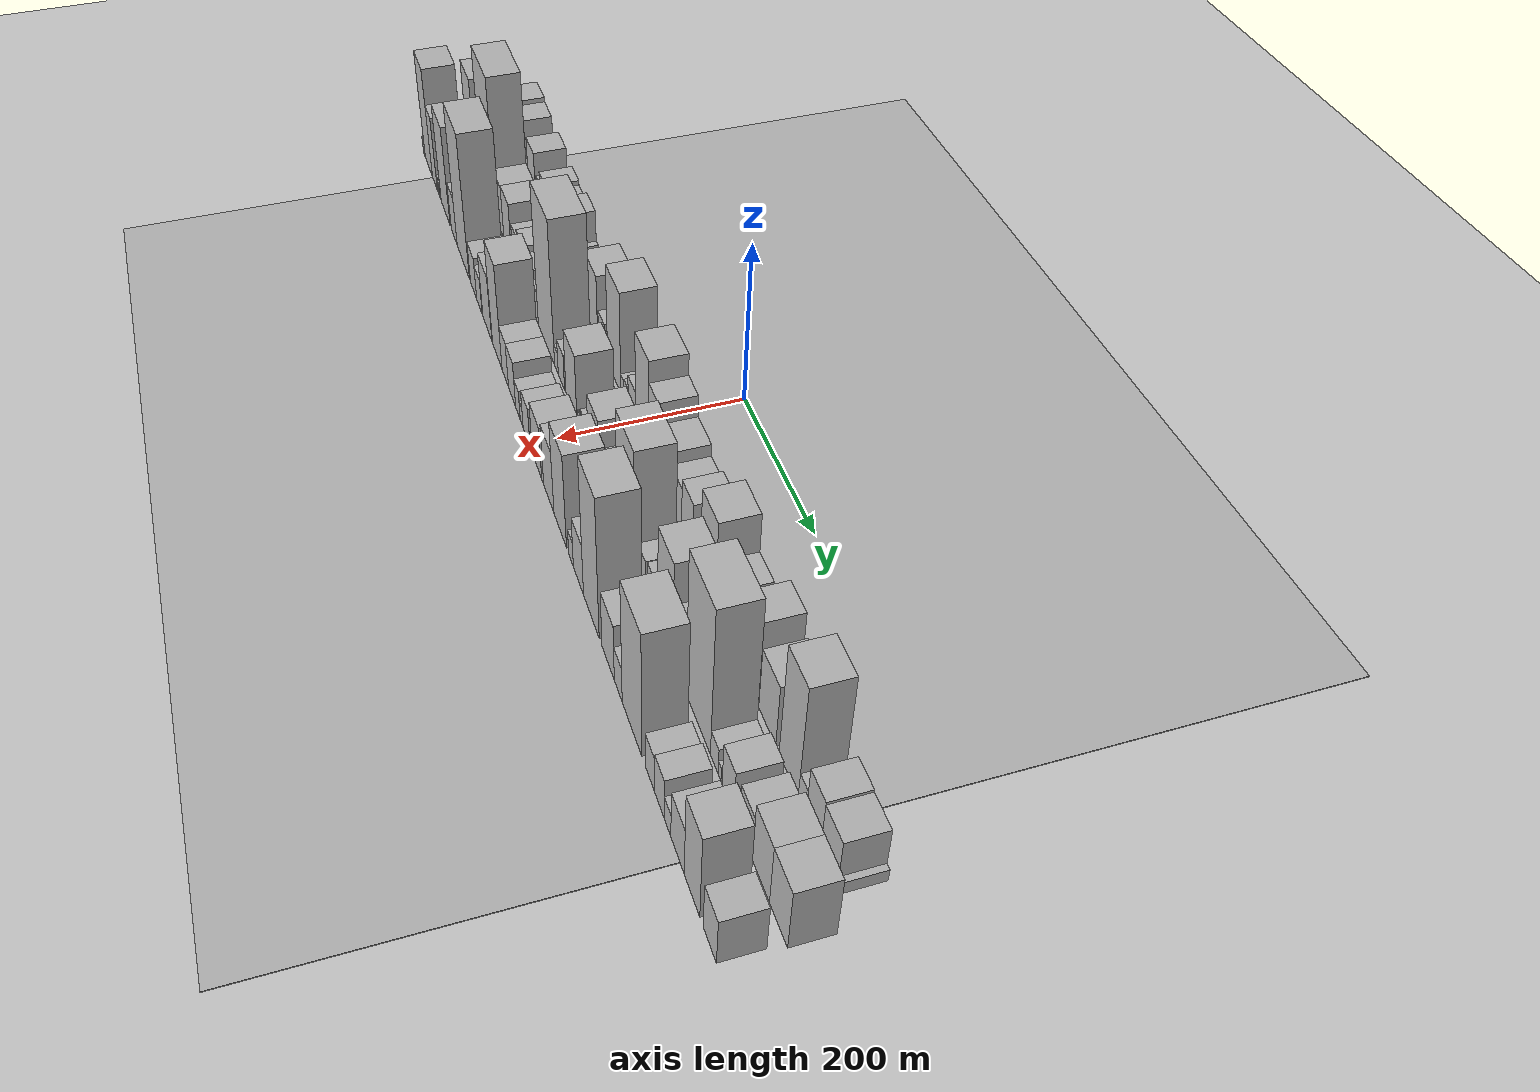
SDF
<?xml version="1.0" encoding="utf-8"?>

<sdf version="1.6">

   <world name="default">

      <gui fullscreen="0">

         <camera name="user_camera">

            <pose>-15 0 4.57585 0 0 0</pose>

            <view_controller>orbit</view_controller>

         </camera>

      </gui>

      <scene>

         <sky>

           <clouds>

             <speed>12</speed>

           </clouds>

         </sky>

         <ambient>0.4 0.4 0.4 1</ambient>

         <background>0.7 0.7 0.7 1</background>

         <shadows>1</shadows>

      </scene>

      <gravity>0 0 -9.8066</gravity>

      <magnetic_field>6e-06 2.3e-05 -4.2e-05</magnetic_field>

      <physics default="0" name="default_physics" type="ode">

         <ode>

            <solver>

               <type>quick</type>

               <iters>10</iters>

               <sor>1.0</sor>

               <use_dynamic_moi_rescaling>0</use_dynamic_moi_rescaling>

            </solver>

            <constraints>

               <cfm>0</cfm>

               <erp>0.2</erp>

               <contact_max_correcting_vel>100</contact_max_correcting_vel>

               <contact_surface_layer>0.001</contact_surface_layer>

            </constraints>

         </ode>

         <max_step_size>0.004</max_step_size>

         <real_time_factor>1</real_time_factor>

         <real_time_update_rate>250</real_time_update_rate>

      </physics>

      <light name="sun" type="directional">

         <cast_shadows>1</cast_shadows>

         <pose>0 0 10 0 0 0</pose>

         <diffuse>0.8 0.8 0.8 1</diffuse>

         <specular>0.2 0.2 0.2 1</specular>

         <attenuation>

            <range>1000</range>

            <constant>0.9</constant>

            <linear>0.01</linear>

            <quadratic>0.001</quadratic>

         </attenuation>

         <direction>-0.5 0.1 -0.9</direction>

      </light>

      <include>

         <name>ground_plane_1</name>

         <uri>model://HANNAS_ground_plane</uri>

         <pose>0 0 0  0 0 0</pose>

      </include>

      <include>

         <name>ground_plane_2</name>

         <uri>model://HANNAS_ground_plane</uri>

         <pose>100 0 0  0 0 0</pose>

      </include>

      <model name="building_1">

         <static>1</static>

         <pose frame="">100.0000 -540.6240 0 0.000000 0.000000 0.000000</pose>

         <link name="link">

            <pose frame="">0 0 37.50 0 0 0</pose>

            <collision name="collision">

               <geometry>

                  <box>

                     <size>40.0000 38.7520 75.0000</size>

                  </box>

               </geometry>

               <max_contacts>10</max_contacts>

               <surface>

                  <contact>

                     <ode/>

                  </contact>

                  <bounce/>

                  <friction>

                     <torsional>

                        <ode/>

                     </torsional>

                     <ode/>

                  </friction>

               </surface>

            </collision>

            <visual name="visual">

               <cast_shadows>0</cast_shadows>

               <geometry>

                  <box>

                     <size>40.0000 38.7520 75.0000</size>

                  </box>

               </geometry>

               <material>

                  <script>

                     <uri>model://HANNAS_wall/materials/scripts</uri>

                     <uri>model://HANNAS_wall/materials/textures</uri>

                     <name>vrc/HANNAS_wall</name>

                  </script>

               </material>

            </visual>

            <self_collide>0</self_collide>

            <enable_wind>0</enable_wind>

            <kinematic>0</kinematic>

         </link>

      </model>

      <model name="building_2">

         <static>1</static>

         <pose frame="">100.0000 -503.2858 0 0.000000 0.000000 0.000000</pose>

         <link name="link">

            <pose frame="">0 0 34.50 0 0 0</pose>

            <collision name="collision">

               <geometry>

                  <box>

                     <size>40.0000 35.9245 69.0000</size>

                  </box>

               </geometry>

               <max_contacts>10</max_contacts>

               <surface>

                  <contact>

                     <ode/>

                  </contact>

                  <bounce/>

                  <friction>

                     <torsional>

                        <ode/>

                     </torsional>

                     <ode/>

                  </friction>

               </surface>

            </collision>

            <visual name="visual">

               <cast_shadows>0</cast_shadows>

               <geometry>

                  <box>

                     <size>40.0000 35.9245 69.0000</size>

                  </box>

               </geometry>

               <material>

                  <script>

                     <uri>model://HANNAS_wall/materials/scripts</uri>

                     <uri>model://HANNAS_wall/materials/textures</uri>

                     <name>vrc/HANNAS_wall</name>

                  </script>

               </material>

            </visual>

            <self_collide>0</self_collide>

            <enable_wind>0</enable_wind>

            <kinematic>0</kinematic>

         </link>

      </model>

      <model name="building_3">

         <static>1</static>

         <pose frame="">100.0000 -478.7070 0 0.000000 0.000000 0.000000</pose>

         <link name="link">

            <pose frame="">0 0 13.50 0 0 0</pose>

            <collision name="collision">

               <geometry>

                  <box>

                     <size>40.0000 13.2330 27.0000</size>

                  </box>

               </geometry>

               <max_contacts>10</max_contacts>

               <surface>

                  <contact>

                     <ode/>

                  </contact>

                  <bounce/>

                  <friction>

                     <torsional>

                        <ode/>

                     </torsional>

                     <ode/>

                  </friction>

               </surface>

            </collision>

            <visual name="visual">

               <cast_shadows>0</cast_shadows>

               <geometry>

                  <box>

                     <size>40.0000 13.2330 27.0000</size>

                  </box>

               </geometry>

               <material>

                  <script>

                     <uri>model://HANNAS_wall/materials/scripts</uri>

                     <uri>model://HANNAS_wall/materials/textures</uri>

                     <name>vrc/HANNAS_wall</name>

                  </script>

               </material>

            </visual>

            <self_collide>0</self_collide>

            <enable_wind>0</enable_wind>

            <kinematic>0</kinematic>

         </link>

      </model>

      <model name="building_4">

         <static>1</static>

         <pose frame="">100.0000 -463.0594 0 0.000000 0.000000 0.000000</pose>

         <link name="link">

            <pose frame="">0 0 18.00 0 0 0</pose>

            <collision name="collision">

               <geometry>

                  <box>

                     <size>40.0000 18.0622 36.0000</size>

                  </box>

               </geometry>

               <max_contacts>10</max_contacts>

               <surface>

                  <contact>

                     <ode/>

                  </contact>

                  <bounce/>

                  <friction>

                     <torsional>

                        <ode/>

                     </torsional>

                     <ode/>

                  </friction>

               </surface>

            </collision>

            <visual name="visual">

               <cast_shadows>0</cast_shadows>

               <geometry>

                  <box>

                     <size>40.0000 18.0622 36.0000</size>

                  </box>

               </geometry>

               <material>

                  <script>

                     <uri>model://HANNAS_wall/materials/scripts</uri>

                     <uri>model://HANNAS_wall/materials/textures</uri>

                     <name>vrc/HANNAS_wall</name>

                  </script>

               </material>

            </visual>

            <self_collide>0</self_collide>

            <enable_wind>0</enable_wind>

            <kinematic>0</kinematic>

         </link>

      </model>

      <model name="building_5">

         <static>1</static>

         <pose frame="">100.0000 -435.4157 0 0.000000 0.000000 0.000000</pose>

         <link name="link">

            <pose frame="">0 0 33.00 0 0 0</pose>

            <collision name="collision">

               <geometry>

                  <box>

                     <size>40.0000 37.2252 66.0000</size>

                  </box>

               </geometry>

               <max_contacts>10</max_contacts>

               <surface>

                  <contact>

                     <ode/>

                  </contact>

                  <bounce/>

                  <friction>

                     <torsional>

                        <ode/>

                     </torsional>

                     <ode/>

                  </friction>

               </surface>

            </collision>

            <visual name="visual">

               <cast_shadows>0</cast_shadows>

               <geometry>

                  <box>

                     <size>40.0000 37.2252 66.0000</size>

                  </box>

               </geometry>

               <material>

                  <script>

                     <uri>model://HANNAS_wall/materials/scripts</uri>

                     <uri>model://HANNAS_wall/materials/textures</uri>

                     <name>vrc/HANNAS_wall</name>

                  </script>

               </material>

            </visual>

            <self_collide>0</self_collide>

            <enable_wind>0</enable_wind>

            <kinematic>0</kinematic>

         </link>

      </model>

      <model name="building_6">

         <static>1</static>

         <pose frame="">100.0000 -400.6879 0 0.000000 0.000000 0.000000</pose>

         <link name="link">

            <pose frame="">0 0 19.50 0 0 0</pose>

            <collision name="collision">

               <geometry>

                  <box>

                     <size>40.0000 20.2305 39.0000</size>

                  </box>

               </geometry>

               <max_contacts>10</max_contacts>

               <surface>

                  <contact>

                     <ode/>

                  </contact>

                  <bounce/>

                  <friction>

                     <torsional>

                        <ode/>

                     </torsional>

                     <ode/>

                  </friction>

               </surface>

            </collision>

            <visual name="visual">

               <cast_shadows>0</cast_shadows>

               <geometry>

                  <box>

                     <size>40.0000 20.2305 39.0000</size>

                  </box>

               </geometry>

               <material>

                  <script>

                     <uri>model://HANNAS_wall/materials/scripts</uri>

                     <uri>model://HANNAS_wall/materials/textures</uri>

                     <name>vrc/HANNAS_wall</name>

                  </script>

               </material>

            </visual>

            <self_collide>0</self_collide>

            <enable_wind>0</enable_wind>

            <kinematic>0</kinematic>

         </link>

      </model>

      <model name="building_7">

         <static>1</static>

         <pose frame="">100.0000 -374.8628 0 0.000000 0.000000 0.000000</pose>

         <link name="link">

            <pose frame="">0 0 28.50 0 0 0</pose>

            <collision name="collision">

               <geometry>

                  <box>

                     <size>40.0000 31.4197 57.0000</size>

                  </box>

               </geometry>

               <max_contacts>10</max_contacts>

               <surface>

                  <contact>

                     <ode/>

                  </contact>

                  <bounce/>

                  <friction>

                     <torsional>

                        <ode/>

                     </torsional>

                     <ode/>

                  </friction>

               </surface>

            </collision>

            <visual name="visual">

               <cast_shadows>0</cast_shadows>

               <geometry>

                  <box>

                     <size>40.0000 31.4197 57.0000</size>

                  </box>

               </geometry>

               <material>

                  <script>

                     <uri>model://HANNAS_wall/materials/scripts</uri>

                     <uri>model://HANNAS_wall/materials/textures</uri>

                     <name>vrc/HANNAS_wall</name>

                  </script>

               </material>

            </visual>

            <self_collide>0</self_collide>

            <enable_wind>0</enable_wind>

            <kinematic>0</kinematic>

         </link>

      </model>

      <model name="building_8">

         <static>1</static>

         <pose frame="">100.0000 -345.2533 0 0.000000 0.000000 0.000000</pose>

         <link name="link">

            <pose frame="">0 0 25.50 0 0 0</pose>

            <collision name="collision">

               <geometry>

                  <box>

                     <size>40.0000 27.7993 51.0000</size>

                  </box>

               </geometry>

               <max_contacts>10</max_contacts>

               <surface>

                  <contact>

                     <ode/>

                  </contact>

                  <bounce/>

                  <friction>

                     <torsional>

                        <ode/>

                     </torsional>

                     <ode/>

                  </friction>

               </surface>

            </collision>

            <visual name="visual">

               <cast_shadows>0</cast_shadows>

               <geometry>

                  <box>

                     <size>40.0000 27.7993 51.0000</size>

                  </box>

               </geometry>

               <material>

                  <script>

                     <uri>model://HANNAS_wall/materials/scripts</uri>

                     <uri>model://HANNAS_wall/materials/textures</uri>

                     <name>vrc/HANNAS_wall</name>

                  </script>

               </material>

            </visual>

            <self_collide>0</self_collide>

            <enable_wind>0</enable_wind>

            <kinematic>0</kinematic>

         </link>

      </model>

      <model name="building_9">

         <static>1</static>

         <pose frame="">100.0000 -305.4927 0 0.000000 0.000000 0.000000</pose>

         <link name="link">

            <pose frame="">0 0 31.50 0 0 0</pose>

            <collision name="collision">

               <geometry>

                  <box>

                     <size>40.0000 37.7221 63.0000</size>

                  </box>

               </geometry>

               <max_contacts>10</max_contacts>

               <surface>

                  <contact>

                     <ode/>

                  </contact>

                  <bounce/>

                  <friction>

                     <torsional>

                        <ode/>

                     </torsional>

                     <ode/>

                  </friction>

               </surface>

            </collision>

            <visual name="visual">

               <cast_shadows>0</cast_shadows>

               <geometry>

                  <box>

                     <size>40.0000 37.7221 63.0000</size>

                  </box>

               </geometry>

               <material>

                  <script>

                     <uri>model://HANNAS_wall/materials/scripts</uri>

                     <uri>model://HANNAS_wall/materials/textures</uri>

                     <name>vrc/HANNAS_wall</name>

                  </script>

               </material>

            </visual>

            <self_collide>0</self_collide>

            <enable_wind>0</enable_wind>

            <kinematic>0</kinematic>

         </link>

      </model>

      <model name="building_10">

         <static>1</static>

         <pose frame="">100.0000 -282.3842 0 0.000000 0.000000 0.000000</pose>

         <link name="link">

            <pose frame="">0 0 10.50 0 0 0</pose>

            <collision name="collision">

               <geometry>

                  <box>

                     <size>40.0000 8.4948 21.0000</size>

                  </box>

               </geometry>

               <max_contacts>10</max_contacts>

               <surface>

                  <contact>

                     <ode/>

                  </contact>

                  <bounce/>

                  <friction>

                     <torsional>

                        <ode/>

                     </torsional>

                     <ode/>

                  </friction>

               </surface>

            </collision>

            <visual name="visual">

               <cast_shadows>0</cast_shadows>

               <geometry>

                  <box>

                     <size>40.0000 8.4948 21.0000</size>

                  </box>

               </geometry>

               <material>

                  <script>

                     <uri>model://HANNAS_wall/materials/scripts</uri>

                     <uri>model://HANNAS_wall/materials/textures</uri>

                     <name>vrc/HANNAS_wall</name>

                  </script>

               </material>

            </visual>

            <self_collide>0</self_collide>

            <enable_wind>0</enable_wind>

            <kinematic>0</kinematic>

         </link>

      </model>

      <model name="building_11">

         <static>1</static>

         <pose frame="">100.0000 -274.6792 0 0.000000 0.000000 0.000000</pose>

         <link name="link">

            <pose frame="">0 0 7.50 0 0 0</pose>

            <collision name="collision">

               <geometry>

                  <box>

                     <size>40.0000 6.9152 15.0000</size>

                  </box>

               </geometry>

               <max_contacts>10</max_contacts>

               <surface>

                  <contact>

                     <ode/>

                  </contact>

                  <bounce/>

                  <friction>

                     <torsional>

                        <ode/>

                     </torsional>

                     <ode/>

                  </friction>

               </surface>

            </collision>

            <visual name="visual">

               <cast_shadows>0</cast_shadows>

               <geometry>

                  <box>

                     <size>40.0000 6.9152 15.0000</size>

                  </box>

               </geometry>

               <material>

                  <script>

                     <uri>model://HANNAS_wall/materials/scripts</uri>

                     <uri>model://HANNAS_wall/materials/textures</uri>

                     <name>vrc/HANNAS_wall</name>

                  </script>

               </material>

            </visual>

            <self_collide>0</self_collide>

            <enable_wind>0</enable_wind>

            <kinematic>0</kinematic>

         </link>

      </model>

      <model name="building_12">

         <static>1</static>

         <pose frame="">100.0000 -212.0638 0 0.000000 0.000000 0.000000</pose>

         <link name="link">

            <pose frame="">0 0 15.00 0 0 0</pose>

            <collision name="collision">

               <geometry>

                  <box>

                     <size>40.0000 17.4385 30.0000</size>

                  </box>

               </geometry>

               <max_contacts>10</max_contacts>

               <surface>

                  <contact>

                     <ode/>

                  </contact>

                  <bounce/>

                  <friction>

                     <torsional>

                        <ode/>

                     </torsional>

                     <ode/>

                  </friction>

               </surface>

            </collision>

            <visual name="visual">

               <cast_shadows>0</cast_shadows>

               <geometry>

                  <box>

                     <size>40.0000 17.4385 30.0000</size>

                  </box>

               </geometry>

               <material>

                  <script>

                     <uri>model://HANNAS_wall/materials/scripts</uri>

                     <uri>model://HANNAS_wall/materials/textures</uri>

                     <name>vrc/HANNAS_wall</name>

                  </script>

               </material>

            </visual>

            <self_collide>0</self_collide>

            <enable_wind>0</enable_wind>

            <kinematic>0</kinematic>

         </link>

      </model>

      <model name="building_13">

         <static>1</static>

         <pose frame="">100.0000 -200.2805 0 0.000000 0.000000 0.000000</pose>

         <link name="link">

            <pose frame="">0 0 7.50 0 0 0</pose>

            <collision name="collision">

               <geometry>

                  <box>

                     <size>40.0000 6.1282 15.0000</size>

                  </box>

               </geometry>

               <max_contacts>10</max_contacts>

               <surface>

                  <contact>

                     <ode/>

                  </contact>

                  <bounce/>

                  <friction>

                     <torsional>

                        <ode/>

                     </torsional>

                     <ode/>

                  </friction>

               </surface>

            </collision>

            <visual name="visual">

               <cast_shadows>0</cast_shadows>

               <geometry>

                  <box>

                     <size>40.0000 6.1282 15.0000</size>

                  </box>

               </geometry>

               <material>

                  <script>

                     <uri>model://HANNAS_wall/materials/scripts</uri>

                     <uri>model://HANNAS_wall/materials/textures</uri>

                     <name>vrc/HANNAS_wall</name>

                  </script>

               </material>

            </visual>

            <self_collide>0</self_collide>

            <enable_wind>0</enable_wind>

            <kinematic>0</kinematic>

         </link>

      </model>

      <model name="building_14">

         <static>1</static>

         <pose frame="">100.0000 -162.4291 0 0.000000 0.000000 0.000000</pose>

         <link name="link">

            <pose frame="">0 0 43.50 0 0 0</pose>

            <collision name="collision">

               <geometry>

                  <box>

                     <size>40.0000 49.5747 87.0000</size>

                  </box>

               </geometry>

               <max_contacts>10</max_contacts>

               <surface>

                  <contact>

                     <ode/>

                  </contact>

                  <bounce/>

                  <friction>

                     <torsional>

                        <ode/>

                     </torsional>

                     <ode/>

                  </friction>

               </surface>

            </collision>

            <visual name="visual">

               <cast_shadows>0</cast_shadows>

               <geometry>

                  <box>

                     <size>40.0000 49.5747 87.0000</size>

                  </box>

               </geometry>

               <material>

                  <script>

                     <uri>model://HANNAS_wall/materials/scripts</uri>

                     <uri>model://HANNAS_wall/materials/textures</uri>

                     <name>vrc/HANNAS_wall</name>

                  </script>

               </material>

            </visual>

            <self_collide>0</self_collide>

            <enable_wind>0</enable_wind>

            <kinematic>0</kinematic>

         </link>

      </model>

      <model name="building_15">

         <static>1</static>

         <pose frame="">100.0000 -120.9237 0 0.000000 0.000000 0.000000</pose>

         <link name="link">

            <pose frame="">0 0 22.50 0 0 0</pose>

            <collision name="collision">

               <geometry>

                  <box>

                     <size>40.0000 25.4361 45.0000</size>

                  </box>

               </geometry>

               <max_contacts>10</max_contacts>

               <surface>

                  <contact>

                     <ode/>

                  </contact>

                  <bounce/>

                  <friction>

                     <torsional>

                        <ode/>

                     </torsional>

                     <ode/>

                  </friction>

               </surface>

            </collision>

            <visual name="visual">

               <cast_shadows>0</cast_shadows>

               <geometry>

                  <box>

                     <size>40.0000 25.4361 45.0000</size>

                  </box>

               </geometry>

               <material>

                  <script>

                     <uri>model://HANNAS_wall/materials/scripts</uri>

                     <uri>model://HANNAS_wall/materials/textures</uri>

                     <name>vrc/HANNAS_wall</name>

                  </script>

               </material>

            </visual>

            <self_collide>0</self_collide>

            <enable_wind>0</enable_wind>

            <kinematic>0</kinematic>

         </link>

      </model>

      <model name="building_16">

         <static>1</static>

         <pose frame="">100.0000 -100.9592 0 0.000000 0.000000 0.000000</pose>

         <link name="link">

            <pose frame="">0 0 7.50 0 0 0</pose>

            <collision name="collision">

               <geometry>

                  <box>

                     <size>40.0000 6.4929 15.0000</size>

                  </box>

               </geometry>

               <max_contacts>10</max_contacts>

               <surface>

                  <contact>

                     <ode/>

                  </contact>

                  <bounce/>

                  <friction>

                     <torsional>

                        <ode/>

                     </torsional>

                     <ode/>

                  </friction>

               </surface>

            </collision>

            <visual name="visual">

               <cast_shadows>0</cast_shadows>

               <geometry>

                  <box>

                     <size>40.0000 6.4929 15.0000</size>

                  </box>

               </geometry>

               <material>

                  <script>

                     <uri>model://HANNAS_wall/materials/scripts</uri>

                     <uri>model://HANNAS_wall/materials/textures</uri>

                     <name>vrc/HANNAS_wall</name>

                  </script>

               </material>

            </visual>

            <self_collide>0</self_collide>

            <enable_wind>0</enable_wind>

            <kinematic>0</kinematic>

         </link>

      </model>

      <model name="building_17">

         <static>1</static>

         <pose frame="">100.0000 -72.6826 0 0.000000 0.000000 0.000000</pose>

         <link name="link">

            <pose frame="">0 0 66.00 0 0 0</pose>

            <collision name="collision">

               <geometry>

                  <box>

                     <size>40.0000 50.0604 132.0000</size>

                  </box>

               </geometry>

               <max_contacts>10</max_contacts>

               <surface>

                  <contact>

                     <ode/>

                  </contact>

                  <bounce/>

                  <friction>

                     <torsional>

                        <ode/>

                     </torsional>

                     <ode/>

                  </friction>

               </surface>

            </collision>

            <visual name="visual">

               <cast_shadows>0</cast_shadows>

               <geometry>

                  <box>

                     <size>40.0000 50.0604 132.0000</size>

                  </box>

               </geometry>

               <material>

                  <script>

                     <uri>model://HANNAS_wall/materials/scripts</uri>

                     <uri>model://HANNAS_wall/materials/textures</uri>

                     <name>vrc/HANNAS_wall</name>

                  </script>

               </material>

            </visual>

            <self_collide>0</self_collide>

            <enable_wind>0</enable_wind>

            <kinematic>0</kinematic>

         </link>

      </model>

      <model name="building_18">

         <static>1</static>

         <pose frame="">100.0000 -41.4615 0 0.000000 0.000000 0.000000</pose>

         <link name="link">

            <pose frame="">0 0 13.50 0 0 0</pose>

            <collision name="collision">

               <geometry>

                  <box>

                     <size>40.0000 12.3819 27.0000</size>

                  </box>

               </geometry>

               <max_contacts>10</max_contacts>

               <surface>

                  <contact>

                     <ode/>

                  </contact>

                  <bounce/>

                  <friction>

                     <torsional>

                        <ode/>

                     </torsional>

                     <ode/>

                  </friction>

               </surface>

            </collision>

            <visual name="visual">

               <cast_shadows>0</cast_shadows>

               <geometry>

                  <box>

                     <size>40.0000 12.3819 27.0000</size>

                  </box>

               </geometry>

               <material>

                  <script>

                     <uri>model://HANNAS_wall/materials/scripts</uri>

                     <uri>model://HANNAS_wall/materials/textures</uri>

                     <name>vrc/HANNAS_wall</name>

                  </script>

               </material>

            </visual>

            <self_collide>0</self_collide>

            <enable_wind>0</enable_wind>

            <kinematic>0</kinematic>

         </link>

      </model>

      <model name="building_19">

         <static>1</static>

         <pose frame="">100.0000 -27.5085 0 0.000000 0.000000 0.000000</pose>

         <link name="link">

            <pose frame="">0 0 15.00 0 0 0</pose>

            <collision name="collision">

               <geometry>

                  <box>

                     <size>40.0000 15.5241 30.0000</size>

                  </box>

               </geometry>

               <max_contacts>10</max_contacts>

               <surface>

                  <contact>

                     <ode/>

                  </contact>

                  <bounce/>

                  <friction>

                     <torsional>

                        <ode/>

                     </torsional>

                     <ode/>

                  </friction>

               </surface>

            </collision>

            <visual name="visual">

               <cast_shadows>0</cast_shadows>

               <geometry>

                  <box>

                     <size>40.0000 15.5241 30.0000</size>

                  </box>

               </geometry>

               <material>

                  <script>

                     <uri>model://HANNAS_wall/materials/scripts</uri>

                     <uri>model://HANNAS_wall/materials/textures</uri>

                     <name>vrc/HANNAS_wall</name>

                  </script>

               </material>

            </visual>

            <self_collide>0</self_collide>

            <enable_wind>0</enable_wind>

            <kinematic>0</kinematic>

         </link>

      </model>

      <model name="building_20">

         <static>1</static>

         <pose frame="">100.0000 -6.3963 0 0.000000 0.000000 0.000000</pose>

         <link name="link">

            <pose frame="">0 0 24.00 0 0 0</pose>

            <collision name="collision">

               <geometry>

                  <box>

                     <size>40.0000 26.7004 48.0000</size>

                  </box>

               </geometry>

               <max_contacts>10</max_contacts>

               <surface>

                  <contact>

                     <ode/>

                  </contact>

                  <bounce/>

                  <friction>

                     <torsional>

                        <ode/>

                     </torsional>

                     <ode/>

                  </friction>

               </surface>

            </collision>

            <visual name="visual">

               <cast_shadows>0</cast_shadows>

               <geometry>

                  <box>

                     <size>40.0000 26.7004 48.0000</size>

                  </box>

               </geometry>

               <material>

                  <script>

                     <uri>model://HANNAS_wall/materials/scripts</uri>

                     <uri>model://HANNAS_wall/materials/textures</uri>

                     <name>vrc/HANNAS_wall</name>

                  </script>

               </material>

            </visual>

            <self_collide>0</self_collide>

            <enable_wind>0</enable_wind>

            <kinematic>0</kinematic>

         </link>

      </model>

      <model name="building_21">

         <static>1</static>

         <pose frame="">100.0000 30.4081 0 0.000000 0.000000 0.000000</pose>

         <link name="link">

            <pose frame="">0 0 63.00 0 0 0</pose>

            <collision name="collision">

               <geometry>

                  <box>

                     <size>40.0000 46.9084 126.0000</size>

                  </box>

               </geometry>

               <max_contacts>10</max_contacts>

               <surface>

                  <contact>

                     <ode/>

                  </contact>

                  <bounce/>

                  <friction>

                     <torsional>

                        <ode/>

                     </torsional>

                     <ode/>

                  </friction>

               </surface>

            </collision>

            <visual name="visual">

               <cast_shadows>0</cast_shadows>

               <geometry>

                  <box>

                     <size>40.0000 46.9084 126.0000</size>

                  </box>

               </geometry>

               <material>

                  <script>

                     <uri>model://HANNAS_wall/materials/scripts</uri>

                     <uri>model://HANNAS_wall/materials/textures</uri>

                     <name>vrc/HANNAS_wall</name>

                  </script>

               </material>

            </visual>

            <self_collide>0</self_collide>

            <enable_wind>0</enable_wind>

            <kinematic>0</kinematic>

         </link>

      </model>

      <model name="building_22">

         <static>1</static>

         <pose frame="">100.0000 69.3866 0 0.000000 0.000000 0.000000</pose>

         <link name="link">

            <pose frame="">0 0 49.50 0 0 0</pose>

            <collision name="collision">

               <geometry>

                  <box>

                     <size>40.0000 31.0486 99.0000</size>

                  </box>

               </geometry>

               <max_contacts>10</max_contacts>

               <surface>

                  <contact>

                     <ode/>

                  </contact>

                  <bounce/>

                  <friction>

                     <torsional>

                        <ode/>

                     </torsional>

                     <ode/>

                  </friction>

               </surface>

            </collision>

            <visual name="visual">

               <cast_shadows>0</cast_shadows>

               <geometry>

                  <box>

                     <size>40.0000 31.0486 99.0000</size>

                  </box>

               </geometry>

               <material>

                  <script>

                     <uri>model://HANNAS_wall/materials/scripts</uri>

                     <uri>model://HANNAS_wall/materials/textures</uri>

                     <name>vrc/HANNAS_wall</name>

                  </script>

               </material>

            </visual>

            <self_collide>0</self_collide>

            <enable_wind>0</enable_wind>

            <kinematic>0</kinematic>

         </link>

      </model>

      <model name="building_23">

         <static>1</static>

         <pose frame="">100.0000 105.3446 0 0.000000 0.000000 0.000000</pose>

         <link name="link">

            <pose frame="">0 0 36.00 0 0 0</pose>

            <collision name="collision">

               <geometry>

                  <box>

                     <size>40.0000 40.8673 72.0000</size>

                  </box>

               </geometry>

               <max_contacts>10</max_contacts>

               <surface>

                  <contact>

                     <ode/>

                  </contact>

                  <bounce/>

                  <friction>

                     <torsional>

                        <ode/>

                     </torsional>

                     <ode/>

                  </friction>

               </surface>

            </collision>

            <visual name="visual">

               <cast_shadows>0</cast_shadows>

               <geometry>

                  <box>

                     <size>40.0000 40.8673 72.0000</size>

                  </box>

               </geometry>

               <material>

                  <script>

                     <uri>model://HANNAS_wall/materials/scripts</uri>

                     <uri>model://HANNAS_wall/materials/textures</uri>

                     <name>vrc/HANNAS_wall</name>

                  </script>

               </material>

            </visual>

            <self_collide>0</self_collide>

            <enable_wind>0</enable_wind>

            <kinematic>0</kinematic>

         </link>

      </model>

      <model name="building_24">

         <static>1</static>

         <pose frame="">100.0000 142.7728 0 0.000000 0.000000 0.000000</pose>

         <link name="link">

            <pose frame="">0 0 28.50 0 0 0</pose>

            <collision name="collision">

               <geometry>

                  <box>

                     <size>40.0000 33.9892 57.0000</size>

                  </box>

               </geometry>

               <max_contacts>10</max_contacts>

               <surface>

                  <contact>

                     <ode/>

                  </contact>

                  <bounce/>

                  <friction>

                     <torsional>

                        <ode/>

                     </torsional>

                     <ode/>

                  </friction>

               </surface>

            </collision>

            <visual name="visual">

               <cast_shadows>0</cast_shadows>

               <geometry>

                  <box>

                     <size>40.0000 33.9892 57.0000</size>

                  </box>

               </geometry>

               <material>

                  <script>

                     <uri>model://HANNAS_wall/materials/scripts</uri>

                     <uri>model://HANNAS_wall/materials/textures</uri>

                     <name>vrc/HANNAS_wall</name>

                  </script>

               </material>

            </visual>

            <self_collide>0</self_collide>

            <enable_wind>0</enable_wind>

            <kinematic>0</kinematic>

         </link>

      </model>

      <model name="building_25">

         <static>1</static>

         <pose frame="">100.0000 177.1389 0 0.000000 0.000000 0.000000</pose>

         <link name="link">

            <pose frame="">0 0 34.50 0 0 0</pose>

            <collision name="collision">

               <geometry>

                  <box>

                     <size>40.0000 34.7431 69.0000</size>

                  </box>

               </geometry>

               <max_contacts>10</max_contacts>

               <surface>

                  <contact>

                     <ode/>

                  </contact>

                  <bounce/>

                  <friction>

                     <torsional>

                        <ode/>

                     </torsional>

                     <ode/>

                  </friction>

               </surface>

            </collision>

            <visual name="visual">

               <cast_shadows>0</cast_shadows>

               <geometry>

                  <box>

                     <size>40.0000 34.7431 69.0000</size>

                  </box>

               </geometry>

               <material>

                  <script>

                     <uri>model://HANNAS_wall/materials/scripts</uri>

                     <uri>model://HANNAS_wall/materials/textures</uri>

                     <name>vrc/HANNAS_wall</name>

                  </script>

               </material>

            </visual>

            <self_collide>0</self_collide>

            <enable_wind>0</enable_wind>

            <kinematic>0</kinematic>

         </link>

      </model>

      <model name="building_26">

         <static>1</static>

         <pose frame="">100.0000 202.4227 0 0.000000 0.000000 0.000000</pose>

         <link name="link">

            <pose frame="">0 0 15.00 0 0 0</pose>

            <collision name="collision">

               <geometry>

                  <box>

                     <size>40.0000 15.8244 30.0000</size>

                  </box>

               </geometry>

               <max_contacts>10</max_contacts>

               <surface>

                  <contact>

                     <ode/>

                  </contact>

                  <bounce/>

                  <friction>

                     <torsional>

                        <ode/>

                     </torsional>

                     <ode/>

                  </friction>

               </surface>

            </collision>

            <visual name="visual">

               <cast_shadows>0</cast_shadows>

               <geometry>

                  <box>

                     <size>40.0000 15.8244 30.0000</size>

                  </box>

               </geometry>

               <material>

                  <script>

                     <uri>model://HANNAS_wall/materials/scripts</uri>

                     <uri>model://HANNAS_wall/materials/textures</uri>

                     <name>vrc/HANNAS_wall</name>

                  </script>

               </material>

            </visual>

            <self_collide>0</self_collide>

            <enable_wind>0</enable_wind>

            <kinematic>0</kinematic>

         </link>

      </model>

      <model name="building_27">

         <static>1</static>

         <pose frame="">100.0000 238.3646 0 0.000000 0.000000 0.000000</pose>

         <link name="link">

            <pose frame="">0 0 55.50 0 0 0</pose>

            <collision name="collision">

               <geometry>

                  <box>

                     <size>40.0000 44.0593 111.0000</size>

                  </box>

               </geometry>

               <max_contacts>10</max_contacts>

               <surface>

                  <contact>

                     <ode/>

                  </contact>

                  <bounce/>

                  <friction>

                     <torsional>

                        <ode/>

                     </torsional>

                     <ode/>

                  </friction>

               </surface>

            </collision>

            <visual name="visual">

               <cast_shadows>0</cast_shadows>

               <geometry>

                  <box>

                     <size>40.0000 44.0593 111.0000</size>

                  </box>

               </geometry>

               <material>

                  <script>

                     <uri>model://HANNAS_wall/materials/scripts</uri>

                     <uri>model://HANNAS_wall/materials/textures</uri>

                     <name>vrc/HANNAS_wall</name>

                  </script>

               </material>

            </visual>

            <self_collide>0</self_collide>

            <enable_wind>0</enable_wind>

            <kinematic>0</kinematic>

         </link>

      </model>

      <model name="building_28">

         <static>1</static>

         <pose frame="">100.0000 279.1129 0 0.000000 0.000000 0.000000</pose>

         <link name="link">

            <pose frame="">0 0 31.50 0 0 0</pose>

            <collision name="collision">

               <geometry>

                  <box>

                     <size>40.0000 37.4374 63.0000</size>

                  </box>

               </geometry>

               <max_contacts>10</max_contacts>

               <surface>

                  <contact>

                     <ode/>

                  </contact>

                  <bounce/>

                  <friction>

                     <torsional>

                        <ode/>

                     </torsional>

                     <ode/>

                  </friction>

               </surface>

            </collision>

            <visual name="visual">

               <cast_shadows>0</cast_shadows>

               <geometry>

                  <box>

                     <size>40.0000 37.4374 63.0000</size>

                  </box>

               </geometry>

               <material>

                  <script>

                     <uri>model://HANNAS_wall/materials/scripts</uri>

                     <uri>model://HANNAS_wall/materials/textures</uri>

                     <name>vrc/HANNAS_wall</name>

                  </script>

               </material>

            </visual>

            <self_collide>0</self_collide>

            <enable_wind>0</enable_wind>

            <kinematic>0</kinematic>

         </link>

      </model>

      <model name="building_29">

         <static>1</static>

         <pose frame="">100.0000 318.3676 0 0.000000 0.000000 0.000000</pose>

         <link name="link">

            <pose frame="">0 0 27.00 0 0 0</pose>

            <collision name="collision">

               <geometry>

                  <box>

                     <size>40.0000 27.0721 54.0000</size>

                  </box>

               </geometry>

               <max_contacts>10</max_contacts>

               <surface>

                  <contact>

                     <ode/>

                  </contact>

                  <bounce/>

                  <friction>

                     <torsional>

                        <ode/>

                     </torsional>

                     <ode/>

                  </friction>

               </surface>

            </collision>

            <visual name="visual">

               <cast_shadows>0</cast_shadows>

               <geometry>

                  <box>

                     <size>40.0000 27.0721 54.0000</size>

                  </box>

               </geometry>

               <material>

                  <script>

                     <uri>model://HANNAS_wall/materials/scripts</uri>

                     <uri>model://HANNAS_wall/materials/textures</uri>

                     <name>vrc/HANNAS_wall</name>

                  </script>

               </material>

            </visual>

            <self_collide>0</self_collide>

            <enable_wind>0</enable_wind>

            <kinematic>0</kinematic>

         </link>

      </model>

      <model name="building_30">

         <static>1</static>

         <pose frame="">100.0000 350.6865 0 0.000000 0.000000 0.000000</pose>

         <link name="link">

            <pose frame="">0 0 51.00 0 0 0</pose>

            <collision name="collision">

               <geometry>

                  <box>

                     <size>40.0000 37.5657 102.0000</size>

                  </box>

               </geometry>

               <max_contacts>10</max_contacts>

               <surface>

                  <contact>

                     <ode/>

                  </contact>

                  <bounce/>

                  <friction>

                     <torsional>

                        <ode/>

                     </torsional>

                     <ode/>

                  </friction>

               </surface>

            </collision>

            <visual name="visual">

               <cast_shadows>0</cast_shadows>

               <geometry>

                  <box>

                     <size>40.0000 37.5657 102.0000</size>

                  </box>

               </geometry>

               <material>

                  <script>

                     <uri>model://HANNAS_wall/materials/scripts</uri>

                     <uri>model://HANNAS_wall/materials/textures</uri>

                     <name>vrc/HANNAS_wall</name>

                  </script>

               </material>

            </visual>

            <self_collide>0</self_collide>

            <enable_wind>0</enable_wind>

            <kinematic>0</kinematic>

         </link>

      </model>

      <model name="building_31">

         <static>1</static>

         <pose frame="">100.0000 397.3536 0 0.000000 0.000000 0.000000</pose>

         <link name="link">

            <pose frame="">0 0 39.00 0 0 0</pose>

            <collision name="collision">

               <geometry>

                  <box>

                     <size>40.0000 41.7685 78.0000</size>

                  </box>

               </geometry>

               <max_contacts>10</max_contacts>

               <surface>

                  <contact>

                     <ode/>

                  </contact>

                  <bounce/>

                  <friction>

                     <torsional>

                        <ode/>

                     </torsional>

                     <ode/>

                  </friction>

               </surface>

            </collision>

            <visual name="visual">

               <cast_shadows>0</cast_shadows>

               <geometry>

                  <box>

                     <size>40.0000 41.7685 78.0000</size>

                  </box>

               </geometry>

               <material>

                  <script>

                     <uri>model://HANNAS_wall/materials/scripts</uri>

                     <uri>model://HANNAS_wall/materials/textures</uri>

                     <name>vrc/HANNAS_wall</name>

                  </script>

               </material>

            </visual>

            <self_collide>0</self_collide>

            <enable_wind>0</enable_wind>

            <kinematic>0</kinematic>

         </link>

      </model>

      <model name="building_32">

         <static>1</static>

         <pose frame="">100.0000 448.4988 0 0.000000 0.000000 0.000000</pose>

         <link name="link">

            <pose frame="">0 0 70.50 0 0 0</pose>

            <collision name="collision">

               <geometry>

                  <box>

                     <size>40.0000 44.5219 141.0000</size>

                  </box>

               </geometry>

               <max_contacts>10</max_contacts>

               <surface>

                  <contact>

                     <ode/>

                  </contact>

                  <bounce/>

                  <friction>

                     <torsional>

                        <ode/>

                     </torsional>

                     <ode/>

                  </friction>

               </surface>

            </collision>

            <visual name="visual">

               <cast_shadows>0</cast_shadows>

               <geometry>

                  <box>

                     <size>40.0000 44.5219 141.0000</size>

                  </box>

               </geometry>

               <material>

                  <script>

                     <uri>model://HANNAS_wall/materials/scripts</uri>

                     <uri>model://HANNAS_wall/materials/textures</uri>

                     <name>vrc/HANNAS_wall</name>

                  </script>

               </material>

            </visual>

            <self_collide>0</self_collide>

            <enable_wind>0</enable_wind>

            <kinematic>0</kinematic>

         </link>

      </model>

      <model name="building_33">

         <static>1</static>

         <pose frame="">100.0000 479.5083 0 0.000000 0.000000 0.000000</pose>

         <link name="link">

            <pose frame="">0 0 16.50 0 0 0</pose>

            <collision name="collision">

               <geometry>

                  <box>

                     <size>40.0000 17.4971 33.0000</size>

                  </box>

               </geometry>

               <max_contacts>10</max_contacts>

               <surface>

                  <contact>

                     <ode/>

                  </contact>

                  <bounce/>

                  <friction>

                     <torsional>

                        <ode/>

                     </torsional>

                     <ode/>

                  </friction>

               </surface>

            </collision>

            <visual name="visual">

               <cast_shadows>0</cast_shadows>

               <geometry>

                  <box>

                     <size>40.0000 17.4971 33.0000</size>

                  </box>

               </geometry>

               <material>

                  <script>

                     <uri>model://HANNAS_wall/materials/scripts</uri>

                     <uri>model://HANNAS_wall/materials/textures</uri>

                     <name>vrc/HANNAS_wall</name>

                  </script>

               </material>

            </visual>

            <self_collide>0</self_collide>

            <enable_wind>0</enable_wind>

            <kinematic>0</kinematic>

         </link>

      </model>

      <model name="building_34">

         <static>1</static>

         <pose frame="">100.0000 504.4014 0 0.000000 0.000000 0.000000</pose>

         <link name="link">

            <pose frame="">0 0 31.50 0 0 0</pose>

            <collision name="collision">

               <geometry>

                  <box>

                     <size>40.0000 32.2890 63.0000</size>

                  </box>

               </geometry>

               <max_contacts>10</max_contacts>

               <surface>

                  <contact>

                     <ode/>

                  </contact>

                  <bounce/>

                  <friction>

                     <torsional>

                        <ode/>

                     </torsional>

                     <ode/>

                  </friction>

               </surface>

            </collision>

            <visual name="visual">

               <cast_shadows>0</cast_shadows>

               <geometry>

                  <box>

                     <size>40.0000 32.2890 63.0000</size>

                  </box>

               </geometry>

               <material>

                  <script>

                     <uri>model://HANNAS_wall/materials/scripts</uri>

                     <uri>model://HANNAS_wall/materials/textures</uri>

                     <name>vrc/HANNAS_wall</name>

                  </script>

               </material>

            </visual>

            <self_collide>0</self_collide>

            <enable_wind>0</enable_wind>

            <kinematic>0</kinematic>

         </link>

      </model>

      <model name="building_35">

         <static>1</static>

         <pose frame="">100.0000 538.3689 0 0.000000 0.000000 0.000000</pose>

         <link name="link">

            <pose frame="">0 0 30.00 0 0 0</pose>

            <collision name="collision">

               <geometry>

                  <box>

                     <size>40.0000 35.6460 60.0000</size>

                  </box>

               </geometry>

               <max_contacts>10</max_contacts>

               <surface>

                  <contact>

                     <ode/>

                  </contact>

                  <bounce/>

                  <friction>

                     <torsional>

                        <ode/>

                     </torsional>

                     <ode/>

                  </friction>

               </surface>

            </collision>

            <visual name="visual">

               <cast_shadows>0</cast_shadows>

               <geometry>

                  <box>

                     <size>40.0000 35.6460 60.0000</size>

                  </box>

               </geometry>

               <material>

                  <script>

                     <uri>model://HANNAS_wall/materials/scripts</uri>

                     <uri>model://HANNAS_wall/materials/textures</uri>

                     <name>vrc/HANNAS_wall</name>

                  </script>

               </material>

            </visual>

            <self_collide>0</self_collide>

            <enable_wind>0</enable_wind>

            <kinematic>0</kinematic>

         </link>

      </model>

      <model name="building_36">

         <static>1</static>

         <pose frame="">100.0000 559.2522 0 0.000000 0.000000 0.000000</pose>

         <link name="link">

            <pose frame="">0 0 7.50 0 0 0</pose>

            <collision name="collision">

               <geometry>

                  <box>

                     <size>40.0000 6.1206 15.0000</size>

                  </box>

               </geometry>

               <max_contacts>10</max_contacts>

               <surface>

                  <contact>

                     <ode/>

                  </contact>

                  <bounce/>

                  <friction>

                     <torsional>

                        <ode/>

                     </torsional>

                     <ode/>

                  </friction>

               </surface>

            </collision>

            <visual name="visual">

               <cast_shadows>0</cast_shadows>

               <geometry>

                  <box>

                     <size>40.0000 6.1206 15.0000</size>

                  </box>

               </geometry>

               <material>

                  <script>

                     <uri>model://HANNAS_wall/materials/scripts</uri>

                     <uri>model://HANNAS_wall/materials/textures</uri>

                     <name>vrc/HANNAS_wall</name>

                  </script>

               </material>

            </visual>

            <self_collide>0</self_collide>

            <enable_wind>0</enable_wind>

            <kinematic>0</kinematic>

         </link>

      </model>

      <model name="building_37">

         <static>1</static>

         <pose frame="">155.0000 -527.5149 0 0.000000 0.000000 0.000000</pose>

         <link name="link">

            <pose frame="">0 0 63.00 0 0 0</pose>

            <collision name="collision">

               <geometry>

                  <box>

                     <size>40.0000 48.9702 126.0000</size>

                  </box>

               </geometry>

               <max_contacts>10</max_contacts>

               <surface>

                  <contact>

                     <ode/>

                  </contact>

                  <bounce/>

                  <friction>

                     <torsional>

                        <ode/>

                     </torsional>

                     <ode/>

                  </friction>

               </surface>

            </collision>

            <visual name="visual">

               <cast_shadows>0</cast_shadows>

               <geometry>

                  <box>

                     <size>40.0000 48.9702 126.0000</size>

                  </box>

               </geometry>

               <material>

                  <script>

                     <uri>model://HANNAS_wall/materials/scripts</uri>

                     <uri>model://HANNAS_wall/materials/textures</uri>

                     <name>vrc/HANNAS_wall</name>

                  </script>

               </material>

            </visual>

            <self_collide>0</self_collide>

            <enable_wind>0</enable_wind>

            <kinematic>0</kinematic>

         </link>

      </model>

      <model name="building_38">

         <static>1</static>

         <pose frame="">155.0000 -496.4810 0 0.000000 0.000000 0.000000</pose>

         <link name="link">

            <pose frame="">0 0 13.50 0 0 0</pose>

            <collision name="collision">

               <geometry>

                  <box>

                     <size>40.0000 13.0975 27.0000</size>

                  </box>

               </geometry>

               <max_contacts>10</max_contacts>

               <surface>

                  <contact>

                     <ode/>

                  </contact>

                  <bounce/>

                  <friction>

                     <torsional>

                        <ode/>

                     </torsional>

                     <ode/>

                  </friction>

               </surface>

            </collision>

            <visual name="visual">

               <cast_shadows>0</cast_shadows>

               <geometry>

                  <box>

                     <size>40.0000 13.0975 27.0000</size>

                  </box>

               </geometry>

               <material>

                  <script>

                     <uri>model://HANNAS_wall/materials/scripts</uri>

                     <uri>model://HANNAS_wall/materials/textures</uri>

                     <name>vrc/HANNAS_wall</name>

                  </script>

               </material>

            </visual>

            <self_collide>0</self_collide>

            <enable_wind>0</enable_wind>

            <kinematic>0</kinematic>

         </link>

      </model>

      <model name="building_39">

         <static>1</static>

         <pose frame="">155.0000 -477.5312 0 0.000000 0.000000 0.000000</pose>

         <link name="link">

            <pose frame="">0 0 7.50 0 0 0</pose>

            <collision name="collision">

               <geometry>

                  <box>

                     <size>40.0000 6.8021 15.0000</size>

                  </box>

               </geometry>

               <max_contacts>10</max_contacts>

               <surface>

                  <contact>

                     <ode/>

                  </contact>

                  <bounce/>

                  <friction>

                     <torsional>

                        <ode/>

                     </torsional>

                     <ode/>

                  </friction>

               </surface>

            </collision>

            <visual name="visual">

               <cast_shadows>0</cast_shadows>

               <geometry>

                  <box>

                     <size>40.0000 6.8021 15.0000</size>

                  </box>

               </geometry>

               <material>

                  <script>

                     <uri>model://HANNAS_wall/materials/scripts</uri>

                     <uri>model://HANNAS_wall/materials/textures</uri>

                     <name>vrc/HANNAS_wall</name>

                  </script>

               </material>

            </visual>

            <self_collide>0</self_collide>

            <enable_wind>0</enable_wind>

            <kinematic>0</kinematic>

         </link>

      </model>

      <model name="building_40">

         <static>1</static>

         <pose frame="">155.0000 -427.5598 0 0.000000 0.000000 0.000000</pose>

         <link name="link">

            <pose frame="">0 0 96.00 0 0 0</pose>

            <collision name="collision">

               <geometry>

                  <box>

                     <size>40.0000 75.1407 192.0000</size>

                  </box>

               </geometry>

               <max_contacts>10</max_contacts>

               <surface>

                  <contact>

                     <ode/>

                  </contact>

                  <bounce/>

                  <friction>

                     <torsional>

                        <ode/>

                     </torsional>

                     <ode/>

                  </friction>

               </surface>

            </collision>

            <visual name="visual">

               <cast_shadows>0</cast_shadows>

               <geometry>

                  <box>

                     <size>40.0000 75.1407 192.0000</size>

                  </box>

               </geometry>

               <material>

                  <script>

                     <uri>model://HANNAS_wall/materials/scripts</uri>

                     <uri>model://HANNAS_wall/materials/textures</uri>

                     <name>vrc/HANNAS_wall</name>

                  </script>

               </material>

            </visual>

            <self_collide>0</self_collide>

            <enable_wind>0</enable_wind>

            <kinematic>0</kinematic>

         </link>

      </model>

      <model name="building_41">

         <static>1</static>

         <pose frame="">155.0000 -370.0305 0 0.000000 0.000000 0.000000</pose>

         <link name="link">

            <pose frame="">0 0 36.00 0 0 0</pose>

            <collision name="collision">

               <geometry>

                  <box>

                     <size>40.0000 39.9179 72.0000</size>

                  </box>

               </geometry>

               <max_contacts>10</max_contacts>

               <surface>

                  <contact>

                     <ode/>

                  </contact>

                  <bounce/>

                  <friction>

                     <torsional>

                        <ode/>

                     </torsional>

                     <ode/>

                  </friction>

               </surface>

            </collision>

            <visual name="visual">

               <cast_shadows>0</cast_shadows>

               <geometry>

                  <box>

                     <size>40.0000 39.9179 72.0000</size>

                  </box>

               </geometry>

               <material>

                  <script>

                     <uri>model://HANNAS_wall/materials/scripts</uri>

                     <uri>model://HANNAS_wall/materials/textures</uri>

                     <name>vrc/HANNAS_wall</name>

                  </script>

               </material>

            </visual>

            <self_collide>0</self_collide>

            <enable_wind>0</enable_wind>

            <kinematic>0</kinematic>

         </link>

      </model>

      <model name="building_42">

         <static>1</static>

         <pose frame="">155.0000 -330.1764 0 0.000000 0.000000 0.000000</pose>

         <link name="link">

            <pose frame="">0 0 37.50 0 0 0</pose>

            <collision name="collision">

               <geometry>

                  <box>

                     <size>40.0000 39.7902 75.0000</size>

                  </box>

               </geometry>

               <max_contacts>10</max_contacts>

               <surface>

                  <contact>

                     <ode/>

                  </contact>

                  <bounce/>

                  <friction>

                     <torsional>

                        <ode/>

                     </torsional>

                     <ode/>

                  </friction>

               </surface>

            </collision>

            <visual name="visual">

               <cast_shadows>0</cast_shadows>

               <geometry>

                  <box>

                     <size>40.0000 39.7902 75.0000</size>

                  </box>

               </geometry>

               <material>

                  <script>

                     <uri>model://HANNAS_wall/materials/scripts</uri>

                     <uri>model://HANNAS_wall/materials/textures</uri>

                     <name>vrc/HANNAS_wall</name>

                  </script>

               </material>

            </visual>

            <self_collide>0</self_collide>

            <enable_wind>0</enable_wind>

            <kinematic>0</kinematic>

         </link>

      </model>

      <model name="building_43">

         <static>1</static>

         <pose frame="">155.0000 -287.9558 0 0.000000 0.000000 0.000000</pose>

         <link name="link">

            <pose frame="">0 0 27.00 0 0 0</pose>

            <collision name="collision">

               <geometry>

                  <box>

                     <size>40.0000 28.6510 54.0000</size>

                  </box>

               </geometry>

               <max_contacts>10</max_contacts>

               <surface>

                  <contact>

                     <ode/>

                  </contact>

                  <bounce/>

                  <friction>

                     <torsional>

                        <ode/>

                     </torsional>

                     <ode/>

                  </friction>

               </surface>

            </collision>

            <visual name="visual">

               <cast_shadows>0</cast_shadows>

               <geometry>

                  <box>

                     <size>40.0000 28.6510 54.0000</size>

                  </box>

               </geometry>

               <material>

                  <script>

                     <uri>model://HANNAS_wall/materials/scripts</uri>

                     <uri>model://HANNAS_wall/materials/textures</uri>

                     <name>vrc/HANNAS_wall</name>

                  </script>

               </material>

            </visual>

            <self_collide>0</self_collide>

            <enable_wind>0</enable_wind>

            <kinematic>0</kinematic>

         </link>

      </model>

      <model name="building_44">

         <static>1</static>

         <pose frame="">155.0000 -256.7858 0 0.000000 0.000000 0.000000</pose>

         <link name="link">

            <pose frame="">0 0 33.00 0 0 0</pose>

            <collision name="collision">

               <geometry>

                  <box>

                     <size>40.0000 33.6891 66.0000</size>

                  </box>

               </geometry>

               <max_contacts>10</max_contacts>

               <surface>

                  <contact>

                     <ode/>

                  </contact>

                  <bounce/>

                  <friction>

                     <torsional>

                        <ode/>

                     </torsional>

                     <ode/>

                  </friction>

               </surface>

            </collision>

            <visual name="visual">

               <cast_shadows>0</cast_shadows>

               <geometry>

                  <box>

                     <size>40.0000 33.6891 66.0000</size>

                  </box>

               </geometry>

               <material>

                  <script>

                     <uri>model://HANNAS_wall/materials/scripts</uri>

                     <uri>model://HANNAS_wall/materials/textures</uri>

                     <name>vrc/HANNAS_wall</name>

                  </script>

               </material>

            </visual>

            <self_collide>0</self_collide>

            <enable_wind>0</enable_wind>

            <kinematic>0</kinematic>

         </link>

      </model>

      <model name="building_45">

         <static>1</static>

         <pose frame="">155.0000 -223.1368 0 0.000000 0.000000 0.000000</pose>

         <link name="link">

            <pose frame="">0 0 28.50 0 0 0</pose>

            <collision name="collision">

               <geometry>

                  <box>

                     <size>40.0000 33.6089 57.0000</size>

                  </box>

               </geometry>

               <max_contacts>10</max_contacts>

               <surface>

                  <contact>

                     <ode/>

                  </contact>

                  <bounce/>

                  <friction>

                     <torsional>

                        <ode/>

                     </torsional>

                     <ode/>

                  </friction>

               </surface>

            </collision>

            <visual name="visual">

               <cast_shadows>0</cast_shadows>

               <geometry>

                  <box>

                     <size>40.0000 33.6089 57.0000</size>

                  </box>

               </geometry>

               <material>

                  <script>

                     <uri>model://HANNAS_wall/materials/scripts</uri>

                     <uri>model://HANNAS_wall/materials/textures</uri>

                     <name>vrc/HANNAS_wall</name>

                  </script>

               </material>

            </visual>

            <self_collide>0</self_collide>

            <enable_wind>0</enable_wind>

            <kinematic>0</kinematic>

         </link>

      </model>

      <model name="building_46">

         <static>1</static>

         <pose frame="">155.0000 -194.4467 0 0.000000 0.000000 0.000000</pose>

         <link name="link">

            <pose frame="">0 0 22.50 0 0 0</pose>

            <collision name="collision">

               <geometry>

                  <box>

                     <size>40.0000 23.7713 45.0000</size>

                  </box>

               </geometry>

               <max_contacts>10</max_contacts>

               <surface>

                  <contact>

                     <ode/>

                  </contact>

                  <bounce/>

                  <friction>

                     <torsional>

                        <ode/>

                     </torsional>

                     <ode/>

                  </friction>

               </surface>

            </collision>

            <visual name="visual">

               <cast_shadows>0</cast_shadows>

               <geometry>

                  <box>

                     <size>40.0000 23.7713 45.0000</size>

                  </box>

               </geometry>

               <material>

                  <script>

                     <uri>model://HANNAS_wall/materials/scripts</uri>

                     <uri>model://HANNAS_wall/materials/textures</uri>

                     <name>vrc/HANNAS_wall</name>

                  </script>

               </material>

            </visual>

            <self_collide>0</self_collide>

            <enable_wind>0</enable_wind>

            <kinematic>0</kinematic>

         </link>

      </model>

      <model name="building_47">

         <static>1</static>

         <pose frame="">155.0000 -146.6544 0 0.000000 0.000000 0.000000</pose>

         <link name="link">

            <pose frame="">0 0 94.50 0 0 0</pose>

            <collision name="collision">

               <geometry>

                  <box>

                     <size>40.0000 71.8134 189.0000</size>

                  </box>

               </geometry>

               <max_contacts>10</max_contacts>

               <surface>

                  <contact>

                     <ode/>

                  </contact>

                  <bounce/>

                  <friction>

                     <torsional>

                        <ode/>

                     </torsional>

                     <ode/>

                  </friction>

               </surface>

            </collision>

            <visual name="visual">

               <cast_shadows>0</cast_shadows>

               <geometry>

                  <box>

                     <size>40.0000 71.8134 189.0000</size>

                  </box>

               </geometry>

               <material>

                  <script>

                     <uri>model://HANNAS_wall/materials/scripts</uri>

                     <uri>model://HANNAS_wall/materials/textures</uri>

                     <name>vrc/HANNAS_wall</name>

                  </script>

               </material>

            </visual>

            <self_collide>0</self_collide>

            <enable_wind>0</enable_wind>

            <kinematic>0</kinematic>

         </link>

      </model>

      <model name="building_48">

         <static>1</static>

         <pose frame="">155.0000 -103.0081 0 0.000000 0.000000 0.000000</pose>

         <link name="link">

            <pose frame="">0 0 15.00 0 0 0</pose>

            <collision name="collision">

               <geometry>

                  <box>

                     <size>40.0000 15.4793 30.0000</size>

                  </box>

               </geometry>

               <max_contacts>10</max_contacts>

               <surface>

                  <contact>

                     <ode/>

                  </contact>

                  <bounce/>

                  <friction>

                     <torsional>

                        <ode/>

                     </torsional>

                     <ode/>

                  </friction>

               </surface>

            </collision>

            <visual name="visual">

               <cast_shadows>0</cast_shadows>

               <geometry>

                  <box>

                     <size>40.0000 15.4793 30.0000</size>

                  </box>

               </geometry>

               <material>

                  <script>

                     <uri>model://HANNAS_wall/materials/scripts</uri>

                     <uri>model://HANNAS_wall/materials/textures</uri>

                     <name>vrc/HANNAS_wall</name>

                  </script>

               </material>

            </visual>

            <self_collide>0</self_collide>

            <enable_wind>0</enable_wind>

            <kinematic>0</kinematic>

         </link>

      </model>

      <model name="building_49">

         <static>1</static>

         <pose frame="">155.0000 -82.1235 0 0.000000 0.000000 0.000000</pose>

         <link name="link">

            <pose frame="">0 0 24.00 0 0 0</pose>

            <collision name="collision">

               <geometry>

                  <box>

                     <size>40.0000 26.2899 48.0000</size>

                  </box>

               </geometry>

               <max_contacts>10</max_contacts>

               <surface>

                  <contact>

                     <ode/>

                  </contact>

                  <bounce/>

                  <friction>

                     <torsional>

                        <ode/>

                     </torsional>

                     <ode/>

                  </friction>

               </surface>

            </collision>

            <visual name="visual">

               <cast_shadows>0</cast_shadows>

               <geometry>

                  <box>

                     <size>40.0000 26.2899 48.0000</size>

                  </box>

               </geometry>

               <material>

                  <script>

                     <uri>model://HANNAS_wall/materials/scripts</uri>

                     <uri>model://HANNAS_wall/materials/textures</uri>

                     <name>vrc/HANNAS_wall</name>

                  </script>

               </material>

            </visual>

            <self_collide>0</self_collide>

            <enable_wind>0</enable_wind>

            <kinematic>0</kinematic>

         </link>

      </model>

      <model name="building_50">

         <static>1</static>

         <pose frame="">155.0000 -40.9794 0 0.000000 0.000000 0.000000</pose>

         <link name="link">

            <pose frame="">0 0 43.50 0 0 0</pose>

            <collision name="collision">

               <geometry>

                  <box>

                     <size>40.0000 43.9984 87.0000</size>

                  </box>

               </geometry>

               <max_contacts>10</max_contacts>

               <surface>

                  <contact>

                     <ode/>

                  </contact>

                  <bounce/>

                  <friction>

                     <torsional>

                        <ode/>

                     </torsional>

                     <ode/>

                  </friction>

               </surface>

            </collision>

            <visual name="visual">

               <cast_shadows>0</cast_shadows>

               <geometry>

                  <box>

                     <size>40.0000 43.9984 87.0000</size>

                  </box>

               </geometry>

               <material>

                  <script>

                     <uri>model://HANNAS_wall/materials/scripts</uri>

                     <uri>model://HANNAS_wall/materials/textures</uri>

                     <name>vrc/HANNAS_wall</name>

                  </script>

               </material>

            </visual>

            <self_collide>0</self_collide>

            <enable_wind>0</enable_wind>

            <kinematic>0</kinematic>

         </link>

      </model>

      <model name="building_51">

         <static>1</static>

         <pose frame="">155.0000 -9.0992 0 0.000000 0.000000 0.000000</pose>

         <link name="link">

            <pose frame="">0 0 10.50 0 0 0</pose>

            <collision name="collision">

               <geometry>

                  <box>

                     <size>40.0000 9.7620 21.0000</size>

                  </box>

               </geometry>

               <max_contacts>10</max_contacts>

               <surface>

                  <contact>

                     <ode/>

                  </contact>

                  <bounce/>

                  <friction>

                     <torsional>

                        <ode/>

                     </torsional>

                     <ode/>

                  </friction>

               </surface>

            </collision>

            <visual name="visual">

               <cast_shadows>0</cast_shadows>

               <geometry>

                  <box>

                     <size>40.0000 9.7620 21.0000</size>

                  </box>

               </geometry>

               <material>

                  <script>

                     <uri>model://HANNAS_wall/materials/scripts</uri>

                     <uri>model://HANNAS_wall/materials/textures</uri>

                     <name>vrc/HANNAS_wall</name>

                  </script>

               </material>

            </visual>

            <self_collide>0</self_collide>

            <enable_wind>0</enable_wind>

            <kinematic>0</kinematic>

         </link>

      </model>

      <model name="building_52">

         <static>1</static>

         <pose frame="">155.0000 4.6129 0 0.000000 0.000000 0.000000</pose>

         <link name="link">

            <pose frame="">0 0 15.00 0 0 0</pose>

            <collision name="collision">

               <geometry>

                  <box>

                     <size>40.0000 17.6623 30.0000</size>

                  </box>

               </geometry>

               <max_contacts>10</max_contacts>

               <surface>

                  <contact>

                     <ode/>

                  </contact>

                  <bounce/>

                  <friction>

                     <torsional>

                        <ode/>

                     </torsional>

                     <ode/>

                  </friction>

               </surface>

            </collision>

            <visual name="visual">

               <cast_shadows>0</cast_shadows>

               <geometry>

                  <box>

                     <size>40.0000 17.6623 30.0000</size>

                  </box>

               </geometry>

               <material>

                  <script>

                     <uri>model://HANNAS_wall/materials/scripts</uri>

                     <uri>model://HANNAS_wall/materials/textures</uri>

                     <name>vrc/HANNAS_wall</name>

                  </script>

               </material>

            </visual>

            <self_collide>0</self_collide>

            <enable_wind>0</enable_wind>

            <kinematic>0</kinematic>

         </link>

      </model>

      <model name="building_53">

         <static>1</static>

         <pose frame="">155.0000 19.4923 0 0.000000 0.000000 0.000000</pose>

         <link name="link">

            <pose frame="">0 0 13.50 0 0 0</pose>

            <collision name="collision">

               <geometry>

                  <box>

                     <size>40.0000 12.0966 27.0000</size>

                  </box>

               </geometry>

               <max_contacts>10</max_contacts>

               <surface>

                  <contact>

                     <ode/>

                  </contact>

                  <bounce/>

                  <friction>

                     <torsional>

                        <ode/>

                     </torsional>

                     <ode/>

                  </friction>

               </surface>

            </collision>

            <visual name="visual">

               <cast_shadows>0</cast_shadows>

               <geometry>

                  <box>

                     <size>40.0000 12.0966 27.0000</size>

                  </box>

               </geometry>

               <material>

                  <script>

                     <uri>model://HANNAS_wall/materials/scripts</uri>

                     <uri>model://HANNAS_wall/materials/textures</uri>

                     <name>vrc/HANNAS_wall</name>

                  </script>

               </material>

            </visual>

            <self_collide>0</self_collide>

            <enable_wind>0</enable_wind>

            <kinematic>0</kinematic>

         </link>

      </model>

      <model name="building_54">

         <static>1</static>

         <pose frame="">155.0000 46.2638 0 0.000000 0.000000 0.000000</pose>

         <link name="link">

            <pose frame="">0 0 37.50 0 0 0</pose>

            <collision name="collision">

               <geometry>

                  <box>

                     <size>40.0000 41.4464 75.0000</size>

                  </box>

               </geometry>

               <max_contacts>10</max_contacts>

               <surface>

                  <contact>

                     <ode/>

                  </contact>

                  <bounce/>

                  <friction>

                     <torsional>

                        <ode/>

                     </torsional>

                     <ode/>

                  </friction>

               </surface>

            </collision>

            <visual name="visual">

               <cast_shadows>0</cast_shadows>

               <geometry>

                  <box>

                     <size>40.0000 41.4464 75.0000</size>

                  </box>

               </geometry>

               <material>

                  <script>

                     <uri>model://HANNAS_wall/materials/scripts</uri>

                     <uri>model://HANNAS_wall/materials/textures</uri>

                     <name>vrc/HANNAS_wall</name>

                  </script>

               </material>

            </visual>

            <self_collide>0</self_collide>

            <enable_wind>0</enable_wind>

            <kinematic>0</kinematic>

         </link>

      </model>

      <model name="building_55">

         <static>1</static>

         <pose frame="">155.0000 77.8366 0 0.000000 0.000000 0.000000</pose>

         <link name="link">

            <pose frame="">0 0 19.50 0 0 0</pose>

            <collision name="collision">

               <geometry>

                  <box>

                     <size>40.0000 21.6991 39.0000</size>

                  </box>

               </geometry>

               <max_contacts>10</max_contacts>

               <surface>

                  <contact>

                     <ode/>

                  </contact>

                  <bounce/>

                  <friction>

                     <torsional>

                        <ode/>

                     </torsional>

                     <ode/>

                  </friction>

               </surface>

            </collision>

            <visual name="visual">

               <cast_shadows>0</cast_shadows>

               <geometry>

                  <box>

                     <size>40.0000 21.6991 39.0000</size>

                  </box>

               </geometry>

               <material>

                  <script>

                     <uri>model://HANNAS_wall/materials/scripts</uri>

                     <uri>model://HANNAS_wall/materials/textures</uri>

                     <name>vrc/HANNAS_wall</name>

                  </script>

               </material>

            </visual>

            <self_collide>0</self_collide>

            <enable_wind>0</enable_wind>

            <kinematic>0</kinematic>

         </link>

      </model>

      <model name="building_56">

         <static>1</static>

         <pose frame="">155.0000 99.1272 0 0.000000 0.000000 0.000000</pose>

         <link name="link">

            <pose frame="">0 0 18.00 0 0 0</pose>

            <collision name="collision">

               <geometry>

                  <box>

                     <size>40.0000 20.8821 36.0000</size>

                  </box>

               </geometry>

               <max_contacts>10</max_contacts>

               <surface>

                  <contact>

                     <ode/>

                  </contact>

                  <bounce/>

                  <friction>

                     <torsional>

                        <ode/>

                     </torsional>

                     <ode/>

                  </friction>

               </surface>

            </collision>

            <visual name="visual">

               <cast_shadows>0</cast_shadows>

               <geometry>

                  <box>

                     <size>40.0000 20.8821 36.0000</size>

                  </box>

               </geometry>

               <material>

                  <script>

                     <uri>model://HANNAS_wall/materials/scripts</uri>

                     <uri>model://HANNAS_wall/materials/textures</uri>

                     <name>vrc/HANNAS_wall</name>

                  </script>

               </material>

            </visual>

            <self_collide>0</self_collide>

            <enable_wind>0</enable_wind>

            <kinematic>0</kinematic>

         </link>

      </model>

      <model name="building_57">

         <static>1</static>

         <pose frame="">155.0000 115.5061 0 0.000000 0.000000 0.000000</pose>

         <link name="link">

            <pose frame="">0 0 13.50 0 0 0</pose>

            <collision name="collision">

               <geometry>

                  <box>

                     <size>40.0000 11.8757 27.0000</size>

                  </box>

               </geometry>

               <max_contacts>10</max_contacts>

               <surface>

                  <contact>

                     <ode/>

                  </contact>

                  <bounce/>

                  <friction>

                     <torsional>

                        <ode/>

                     </torsional>

                     <ode/>

                  </friction>

               </surface>

            </collision>

            <visual name="visual">

               <cast_shadows>0</cast_shadows>

               <geometry>

                  <box>

                     <size>40.0000 11.8757 27.0000</size>

                  </box>

               </geometry>

               <material>

                  <script>

                     <uri>model://HANNAS_wall/materials/scripts</uri>

                     <uri>model://HANNAS_wall/materials/textures</uri>

                     <name>vrc/HANNAS_wall</name>

                  </script>

               </material>

            </visual>

            <self_collide>0</self_collide>

            <enable_wind>0</enable_wind>

            <kinematic>0</kinematic>

         </link>

      </model>

      <model name="building_58">

         <static>1</static>

         <pose frame="">155.0000 160.7035 0 0.000000 0.000000 0.000000</pose>

         <link name="link">

            <pose frame="">0 0 73.50 0 0 0</pose>

            <collision name="collision">

               <geometry>

                  <box>

                     <size>40.0000 58.5192 147.0000</size>

                  </box>

               </geometry>

               <max_contacts>10</max_contacts>

               <surface>

                  <contact>

                     <ode/>

                  </contact>

                  <bounce/>

                  <friction>

                     <torsional>

                        <ode/>

                     </torsional>

                     <ode/>

                  </friction>

               </surface>

            </collision>

            <visual name="visual">

               <cast_shadows>0</cast_shadows>

               <geometry>

                  <box>

                     <size>40.0000 58.5192 147.0000</size>

                  </box>

               </geometry>

               <material>

                  <script>

                     <uri>model://HANNAS_wall/materials/scripts</uri>

                     <uri>model://HANNAS_wall/materials/textures</uri>

                     <name>vrc/HANNAS_wall</name>

                  </script>

               </material>

            </visual>

            <self_collide>0</self_collide>

            <enable_wind>0</enable_wind>

            <kinematic>0</kinematic>

         </link>

      </model>

      <model name="building_59">

         <static>1</static>

         <pose frame="">155.0000 212.0692 0 0.000000 0.000000 0.000000</pose>

         <link name="link">

            <pose frame="">0 0 21.00 0 0 0</pose>

            <collision name="collision">

               <geometry>

                  <box>

                     <size>40.0000 24.2121 42.0000</size>

                  </box>

               </geometry>

               <max_contacts>10</max_contacts>

               <surface>

                  <contact>

                     <ode/>

                  </contact>

                  <bounce/>

                  <friction>

                     <torsional>

                        <ode/>

                     </torsional>

                     <ode/>

                  </friction>

               </surface>

            </collision>

            <visual name="visual">

               <cast_shadows>0</cast_shadows>

               <geometry>

                  <box>

                     <size>40.0000 24.2121 42.0000</size>

                  </box>

               </geometry>

               <material>

                  <script>

                     <uri>model://HANNAS_wall/materials/scripts</uri>

                     <uri>model://HANNAS_wall/materials/textures</uri>

                     <name>vrc/HANNAS_wall</name>

                  </script>

               </material>

            </visual>

            <self_collide>0</self_collide>

            <enable_wind>0</enable_wind>

            <kinematic>0</kinematic>

         </link>

      </model>

      <model name="building_60">

         <static>1</static>

         <pose frame="">155.0000 242.2982 0 0.000000 0.000000 0.000000</pose>

         <link name="link">

            <pose frame="">0 0 24.00 0 0 0</pose>

            <collision name="collision">

               <geometry>

                  <box>

                     <size>40.0000 24.2459 48.0000</size>

                  </box>

               </geometry>

               <max_contacts>10</max_contacts>

               <surface>

                  <contact>

                     <ode/>

                  </contact>

                  <bounce/>

                  <friction>

                     <torsional>

                        <ode/>

                     </torsional>

                     <ode/>

                  </friction>

               </surface>

            </collision>

            <visual name="visual">

               <cast_shadows>0</cast_shadows>

               <geometry>

                  <box>

                     <size>40.0000 24.2459 48.0000</size>

                  </box>

               </geometry>

               <material>

                  <script>

                     <uri>model://HANNAS_wall/materials/scripts</uri>

                     <uri>model://HANNAS_wall/materials/textures</uri>

                     <name>vrc/HANNAS_wall</name>

                  </script>

               </material>

            </visual>

            <self_collide>0</self_collide>

            <enable_wind>0</enable_wind>

            <kinematic>0</kinematic>

         </link>

      </model>

      <model name="building_61">

         <static>1</static>

         <pose frame="">155.0000 258.1698 0 0.000000 0.000000 0.000000</pose>

         <link name="link">

            <pose frame="">0 0 9.00 0 0 0</pose>

            <collision name="collision">

               <geometry>

                  <box>

                     <size>40.0000 7.4972 18.0000</size>

                  </box>

               </geometry>

               <max_contacts>10</max_contacts>

               <surface>

                  <contact>

                     <ode/>

                  </contact>

                  <bounce/>

                  <friction>

                     <torsional>

                        <ode/>

                     </torsional>

                     <ode/>

                  </friction>

               </surface>

            </collision>

            <visual name="visual">

               <cast_shadows>0</cast_shadows>

               <geometry>

                  <box>

                     <size>40.0000 7.4972 18.0000</size>

                  </box>

               </geometry>

               <material>

                  <script>

                     <uri>model://HANNAS_wall/materials/scripts</uri>

                     <uri>model://HANNAS_wall/materials/textures</uri>

                     <name>vrc/HANNAS_wall</name>

                  </script>

               </material>

            </visual>

            <self_collide>0</self_collide>

            <enable_wind>0</enable_wind>

            <kinematic>0</kinematic>

         </link>

      </model>

      <model name="building_62">

         <static>1</static>

         <pose frame="">155.0000 284.5172 0 0.000000 0.000000 0.000000</pose>

         <link name="link">

            <pose frame="">0 0 63.00 0 0 0</pose>

            <collision name="collision">

               <geometry>

                  <box>

                     <size>40.0000 45.1977 126.0000</size>

                  </box>

               </geometry>

               <max_contacts>10</max_contacts>

               <surface>

                  <contact>

                     <ode/>

                  </contact>

                  <bounce/>

                  <friction>

                     <torsional>

                        <ode/>

                     </torsional>

                     <ode/>

                  </friction>

               </surface>

            </collision>

            <visual name="visual">

               <cast_shadows>0</cast_shadows>

               <geometry>

                  <box>

                     <size>40.0000 45.1977 126.0000</size>

                  </box>

               </geometry>

               <material>

                  <script>

                     <uri>model://HANNAS_wall/materials/scripts</uri>

                     <uri>model://HANNAS_wall/materials/textures</uri>

                     <name>vrc/HANNAS_wall</name>

                  </script>

               </material>

            </visual>

            <self_collide>0</self_collide>

            <enable_wind>0</enable_wind>

            <kinematic>0</kinematic>

         </link>

      </model>

      <model name="building_63">

         <static>1</static>

         <pose frame="">155.0000 325.9085 0 0.000000 0.000000 0.000000</pose>

         <link name="link">

            <pose frame="">0 0 37.50 0 0 0</pose>

            <collision name="collision">

               <geometry>

                  <box>

                     <size>40.0000 37.5848 75.0000</size>

                  </box>

               </geometry>

               <max_contacts>10</max_contacts>

               <surface>

                  <contact>

                     <ode/>

                  </contact>

                  <bounce/>

                  <friction>

                     <torsional>

                        <ode/>

                     </torsional>

                     <ode/>

                  </friction>

               </surface>

            </collision>

            <visual name="visual">

               <cast_shadows>0</cast_shadows>

               <geometry>

                  <box>

                     <size>40.0000 37.5848 75.0000</size>

                  </box>

               </geometry>

               <material>

                  <script>

                     <uri>model://HANNAS_wall/materials/scripts</uri>

                     <uri>model://HANNAS_wall/materials/textures</uri>

                     <name>vrc/HANNAS_wall</name>

                  </script>

               </material>

            </visual>

            <self_collide>0</self_collide>

            <enable_wind>0</enable_wind>

            <kinematic>0</kinematic>

         </link>

      </model>

      <model name="building_64">

         <static>1</static>

         <pose frame="">155.0000 377.6794 0 0.000000 0.000000 0.000000</pose>

         <link name="link">

            <pose frame="">0 0 91.50 0 0 0</pose>

            <collision name="collision">

               <geometry>

                  <box>

                     <size>40.0000 65.9570 183.0000</size>

                  </box>

               </geometry>

               <max_contacts>10</max_contacts>

               <surface>

                  <contact>

                     <ode/>

                  </contact>

                  <bounce/>

                  <friction>

                     <torsional>

                        <ode/>

                     </torsional>

                     <ode/>

                  </friction>

               </surface>

            </collision>

            <visual name="visual">

               <cast_shadows>0</cast_shadows>

               <geometry>

                  <box>

                     <size>40.0000 65.9570 183.0000</size>

                  </box>

               </geometry>

               <material>

                  <script>

                     <uri>model://HANNAS_wall/materials/scripts</uri>

                     <uri>model://HANNAS_wall/materials/textures</uri>

                     <name>vrc/HANNAS_wall</name>

                  </script>

               </material>

            </visual>

            <self_collide>0</self_collide>

            <enable_wind>0</enable_wind>

            <kinematic>0</kinematic>

         </link>

      </model>

      <model name="building_65">

         <static>1</static>

         <pose frame="">155.0000 420.5182 0 0.000000 0.000000 0.000000</pose>

         <link name="link">

            <pose frame="">0 0 16.50 0 0 0</pose>

            <collision name="collision">

               <geometry>

                  <box>

                     <size>40.0000 19.7208 33.0000</size>

                  </box>

               </geometry>

               <max_contacts>10</max_contacts>

               <surface>

                  <contact>

                     <ode/>

                  </contact>

                  <bounce/>

                  <friction>

                     <torsional>

                        <ode/>

                     </torsional>

                     <ode/>

                  </friction>

               </surface>

            </collision>

            <visual name="visual">

               <cast_shadows>0</cast_shadows>

               <geometry>

                  <box>

                     <size>40.0000 19.7208 33.0000</size>

                  </box>

               </geometry>

               <material>

                  <script>

                     <uri>model://HANNAS_wall/materials/scripts</uri>

                     <uri>model://HANNAS_wall/materials/textures</uri>

                     <name>vrc/HANNAS_wall</name>

                  </script>

               </material>

            </visual>

            <self_collide>0</self_collide>

            <enable_wind>0</enable_wind>

            <kinematic>0</kinematic>

         </link>

      </model>

      <model name="building_66">

         <static>1</static>

         <pose frame="">155.0000 434.0667 0 0.000000 0.000000 0.000000</pose>

         <link name="link">

            <pose frame="">0 0 9.00 0 0 0</pose>

            <collision name="collision">

               <geometry>

                  <box>

                     <size>40.0000 7.3762 18.0000</size>

                  </box>

               </geometry>

               <max_contacts>10</max_contacts>

               <surface>

                  <contact>

                     <ode/>

                  </contact>

                  <bounce/>

                  <friction>

                     <torsional>

                        <ode/>

                     </torsional>

                     <ode/>

                  </friction>

               </surface>

            </collision>

            <visual name="visual">

               <cast_shadows>0</cast_shadows>

               <geometry>

                  <box>

                     <size>40.0000 7.3762 18.0000</size>

                  </box>

               </geometry>

               <material>

                  <script>

                     <uri>model://HANNAS_wall/materials/scripts</uri>

                     <uri>model://HANNAS_wall/materials/textures</uri>

                     <name>vrc/HANNAS_wall</name>

                  </script>

               </material>

            </visual>

            <self_collide>0</self_collide>

            <enable_wind>0</enable_wind>

            <kinematic>0</kinematic>

         </link>

      </model>

      <model name="building_67">

         <static>1</static>

         <pose frame="">155.0000 455.4434 0 0.000000 0.000000 0.000000</pose>

         <link name="link">

            <pose frame="">0 0 27.00 0 0 0</pose>

            <collision name="collision">

               <geometry>

                  <box>

                     <size>40.0000 29.3773 54.0000</size>

                  </box>

               </geometry>

               <max_contacts>10</max_contacts>

               <surface>

                  <contact>

                     <ode/>

                  </contact>

                  <bounce/>

                  <friction>

                     <torsional>

                        <ode/>

                     </torsional>

                     <ode/>

                  </friction>

               </surface>

            </collision>

            <visual name="visual">

               <cast_shadows>0</cast_shadows>

               <geometry>

                  <box>

                     <size>40.0000 29.3773 54.0000</size>

                  </box>

               </geometry>

               <material>

                  <script>

                     <uri>model://HANNAS_wall/materials/scripts</uri>

                     <uri>model://HANNAS_wall/materials/textures</uri>

                     <name>vrc/HANNAS_wall</name>

                  </script>

               </material>

            </visual>

            <self_collide>0</self_collide>

            <enable_wind>0</enable_wind>

            <kinematic>0</kinematic>

         </link>

      </model>

      <model name="building_68">

         <static>1</static>

         <pose frame="">155.0000 477.7358 0 0.000000 0.000000 0.000000</pose>

         <link name="link">

            <pose frame="">0 0 10.50 0 0 0</pose>

            <collision name="collision">

               <geometry>

                  <box>

                     <size>40.0000 9.2075 21.0000</size>

                  </box>

               </geometry>

               <max_contacts>10</max_contacts>

               <surface>

                  <contact>

                     <ode/>

                  </contact>

                  <bounce/>

                  <friction>

                     <torsional>

                        <ode/>

                     </torsional>

                     <ode/>

                  </friction>

               </surface>

            </collision>

            <visual name="visual">

               <cast_shadows>0</cast_shadows>

               <geometry>

                  <box>

                     <size>40.0000 9.2075 21.0000</size>

                  </box>

               </geometry>

               <material>

                  <script>

                     <uri>model://HANNAS_wall/materials/scripts</uri>

                     <uri>model://HANNAS_wall/materials/textures</uri>

                     <name>vrc/HANNAS_wall</name>

                  </script>

               </material>

            </visual>

            <self_collide>0</self_collide>

            <enable_wind>0</enable_wind>

            <kinematic>0</kinematic>

         </link>

      </model>

      <model name="building_69">

         <static>1</static>

         <pose frame="">155.0000 498.4529 0 0.000000 0.000000 0.000000</pose>

         <link name="link">

            <pose frame="">0 0 28.50 0 0 0</pose>

            <collision name="collision">

               <geometry>

                  <box>

                     <size>40.0000 32.2268 57.0000</size>

                  </box>

               </geometry>

               <max_contacts>10</max_contacts>

               <surface>

                  <contact>

                     <ode/>

                  </contact>

                  <bounce/>

                  <friction>

                     <torsional>

                        <ode/>

                     </torsional>

                     <ode/>

                  </friction>

               </surface>

            </collision>

            <visual name="visual">

               <cast_shadows>0</cast_shadows>

               <geometry>

                  <box>

                     <size>40.0000 32.2268 57.0000</size>

                  </box>

               </geometry>

               <material>

                  <script>

                     <uri>model://HANNAS_wall/materials/scripts</uri>

                     <uri>model://HANNAS_wall/materials/textures</uri>

                     <name>vrc/HANNAS_wall</name>

                  </script>

               </material>

            </visual>

            <self_collide>0</self_collide>

            <enable_wind>0</enable_wind>

            <kinematic>0</kinematic>

         </link>

      </model>

      <model name="building_70">

         <static>1</static>

         <pose frame="">155.0000 533.9598 0 0.000000 0.000000 0.000000</pose>

         <link name="link">

            <pose frame="">0 0 37.50 0 0 0</pose>

            <collision name="collision">

               <geometry>

                  <box>

                     <size>40.0000 38.7869 75.0000</size>

                  </box>

               </geometry>

               <max_contacts>10</max_contacts>

               <surface>

                  <contact>

                     <ode/>

                  </contact>

                  <bounce/>

                  <friction>

                     <torsional>

                        <ode/>

                     </torsional>

                     <ode/>

                  </friction>

               </surface>

            </collision>

            <visual name="visual">

               <cast_shadows>0</cast_shadows>

               <geometry>

                  <box>

                     <size>40.0000 38.7869 75.0000</size>

                  </box>

               </geometry>

               <material>

                  <script>

                     <uri>model://HANNAS_wall/materials/scripts</uri>

                     <uri>model://HANNAS_wall/materials/textures</uri>

                     <name>vrc/HANNAS_wall</name>

                  </script>

               </material>

            </visual>

            <self_collide>0</self_collide>

            <enable_wind>0</enable_wind>

            <kinematic>0</kinematic>

         </link>

      </model>

      <model name="building_71">

         <static>1</static>

         <pose frame="">155.0000 573.1449 0 0.000000 0.000000 0.000000</pose>

         <link name="link">

            <pose frame="">0 0 37.50 0 0 0</pose>

            <collision name="collision">

               <geometry>

                  <box>

                     <size>40.0000 39.5834 75.0000</size>

                  </box>

               </geometry>

               <max_contacts>10</max_contacts>

               <surface>

                  <contact>

                     <ode/>

                  </contact>

                  <bounce/>

                  <friction>

                     <torsional>

                        <ode/>

                     </torsional>

                     <ode/>

                  </friction>

               </surface>

            </collision>

            <visual name="visual">

               <cast_shadows>0</cast_shadows>

               <geometry>

                  <box>

                     <size>40.0000 39.5834 75.0000</size>

                  </box>

               </geometry>

               <material>

                  <script>

                     <uri>model://HANNAS_wall/materials/scripts</uri>

                     <uri>model://HANNAS_wall/materials/textures</uri>

                     <name>vrc/HANNAS_wall</name>

                  </script>

               </material>

            </visual>

            <self_collide>0</self_collide>

            <enable_wind>0</enable_wind>

            <kinematic>0</kinematic>

         </link>

      </model>

      <model name="building_72">

         <static>1</static>

         <pose frame="">210.0000 -554.0187 0 0.000000 0.000000 0.000000</pose>

         <link name="link">

            <pose frame="">0 0 12.00 0 0 0</pose>

            <collision name="collision">

               <geometry>

                  <box>

                     <size>40.0000 11.9625 24.0000</size>

                  </box>

               </geometry>

               <max_contacts>10</max_contacts>

               <surface>

                  <contact>

                     <ode/>

                  </contact>

                  <bounce/>

                  <friction>

                     <torsional>

                        <ode/>

                     </torsional>

                     <ode/>

                  </friction>

               </surface>

            </collision>

            <visual name="visual">

               <cast_shadows>0</cast_shadows>

               <geometry>

                  <box>

                     <size>40.0000 11.9625 24.0000</size>

                  </box>

               </geometry>

               <material>

                  <script>

                     <uri>model://HANNAS_wall/materials/scripts</uri>

                     <uri>model://HANNAS_wall/materials/textures</uri>

                     <name>vrc/HANNAS_wall</name>

                  </script>

               </material>

            </visual>

            <self_collide>0</self_collide>

            <enable_wind>0</enable_wind>

            <kinematic>0</kinematic>

         </link>

      </model>

      <model name="building_73">

         <static>1</static>

         <pose frame="">210.0000 -524.6686 0 0.000000 0.000000 0.000000</pose>

         <link name="link">

            <pose frame="">0 0 75.00 0 0 0</pose>

            <collision name="collision">

               <geometry>

                  <box>

                     <size>40.0000 46.7378 150.0000</size>

                  </box>

               </geometry>

               <max_contacts>10</max_contacts>

               <surface>

                  <contact>

                     <ode/>

                  </contact>

                  <bounce/>

                  <friction>

                     <torsional>

                        <ode/>

                     </torsional>

                     <ode/>

                  </friction>

               </surface>

            </collision>

            <visual name="visual">

               <cast_shadows>0</cast_shadows>

               <geometry>

                  <box>

                     <size>40.0000 46.7378 150.0000</size>

                  </box>

               </geometry>

               <material>

                  <script>

                     <uri>model://HANNAS_wall/materials/scripts</uri>

                     <uri>model://HANNAS_wall/materials/textures</uri>

                     <name>vrc/HANNAS_wall</name>

                  </script>

               </material>

            </visual>

            <self_collide>0</self_collide>

            <enable_wind>0</enable_wind>

            <kinematic>0</kinematic>

         </link>

      </model>

      <model name="building_74">

         <static>1</static>

         <pose frame="">210.0000 -485.9888 0 0.000000 0.000000 0.000000</pose>

         <link name="link">

            <pose frame="">0 0 51.00 0 0 0</pose>

            <collision name="collision">

               <geometry>

                  <box>

                     <size>40.0000 30.6217 102.0000</size>

                  </box>

               </geometry>

               <max_contacts>10</max_contacts>

               <surface>

                  <contact>

                     <ode/>

                  </contact>

                  <bounce/>

                  <friction>

                     <torsional>

                        <ode/>

                     </torsional>

                     <ode/>

                  </friction>

               </surface>

            </collision>

            <visual name="visual">

               <cast_shadows>0</cast_shadows>

               <geometry>

                  <box>

                     <size>40.0000 30.6217 102.0000</size>

                  </box>

               </geometry>

               <material>

                  <script>

                     <uri>model://HANNAS_wall/materials/scripts</uri>

                     <uri>model://HANNAS_wall/materials/textures</uri>

                     <name>vrc/HANNAS_wall</name>

                  </script>

               </material>

            </visual>

            <self_collide>0</self_collide>

            <enable_wind>0</enable_wind>

            <kinematic>0</kinematic>

         </link>

      </model>

      <model name="building_75">

         <static>1</static>

         <pose frame="">210.0000 -465.7346 0 0.000000 0.000000 0.000000</pose>

         <link name="link">

            <pose frame="">0 0 12.00 0 0 0</pose>

            <collision name="collision">

               <geometry>

                  <box>

                     <size>40.0000 9.8868 24.0000</size>

                  </box>

               </geometry>

               <max_contacts>10</max_contacts>

               <surface>

                  <contact>

                     <ode/>

                  </contact>

                  <bounce/>

                  <friction>

                     <torsional>

                        <ode/>

                     </torsional>

                     <ode/>

                  </friction>

               </surface>

            </collision>

            <visual name="visual">

               <cast_shadows>0</cast_shadows>

               <geometry>

                  <box>

                     <size>40.0000 9.8868 24.0000</size>

                  </box>

               </geometry>

               <material>

                  <script>

                     <uri>model://HANNAS_wall/materials/scripts</uri>

                     <uri>model://HANNAS_wall/materials/textures</uri>

                     <name>vrc/HANNAS_wall</name>

                  </script>

               </material>

            </visual>

            <self_collide>0</self_collide>

            <enable_wind>0</enable_wind>

            <kinematic>0</kinematic>

         </link>

      </model>

      <model name="building_76">

         <static>1</static>

         <pose frame="">210.0000 -456.0236 0 0.000000 0.000000 0.000000</pose>

         <link name="link">

            <pose frame="">0 0 10.50 0 0 0</pose>

            <collision name="collision">

               <geometry>

                  <box>

                     <size>40.0000 9.5352 21.0000</size>

                  </box>

               </geometry>

               <max_contacts>10</max_contacts>

               <surface>

                  <contact>

                     <ode/>

                  </contact>

                  <bounce/>

                  <friction>

                     <torsional>

                        <ode/>

                     </torsional>

                     <ode/>

                  </friction>

               </surface>

            </collision>

            <visual name="visual">

               <cast_shadows>0</cast_shadows>

               <geometry>

                  <box>

                     <size>40.0000 9.5352 21.0000</size>

                  </box>

               </geometry>

               <material>

                  <script>

                     <uri>model://HANNAS_wall/materials/scripts</uri>

                     <uri>model://HANNAS_wall/materials/textures</uri>

                     <name>vrc/HANNAS_wall</name>

                  </script>

               </material>

            </visual>

            <self_collide>0</self_collide>

            <enable_wind>0</enable_wind>

            <kinematic>0</kinematic>

         </link>

      </model>

      <model name="building_77">

         <static>1</static>

         <pose frame="">210.0000 -420.3888 0 0.000000 0.000000 0.000000</pose>

         <link name="link">

            <pose frame="">0 0 67.50 0 0 0</pose>

            <collision name="collision">

               <geometry>

                  <box>

                     <size>40.0000 53.7343 135.0000</size>

                  </box>

               </geometry>

               <max_contacts>10</max_contacts>

               <surface>

                  <contact>

                     <ode/>

                  </contact>

                  <bounce/>

                  <friction>

                     <torsional>

                        <ode/>

                     </torsional>

                     <ode/>

                  </friction>

               </surface>

            </collision>

            <visual name="visual">

               <cast_shadows>0</cast_shadows>

               <geometry>

                  <box>

                     <size>40.0000 53.7343 135.0000</size>

                  </box>

               </geometry>

               <material>

                  <script>

                     <uri>model://HANNAS_wall/materials/scripts</uri>

                     <uri>model://HANNAS_wall/materials/textures</uri>

                     <name>vrc/HANNAS_wall</name>

                  </script>

               </material>

            </visual>

            <self_collide>0</self_collide>

            <enable_wind>0</enable_wind>

            <kinematic>0</kinematic>

         </link>

      </model>

      <model name="building_78">

         <static>1</static>

         <pose frame="">210.0000 -369.7968 0 0.000000 0.000000 0.000000</pose>

         <link name="link">

            <pose frame="">0 0 33.00 0 0 0</pose>

            <collision name="collision">

               <geometry>

                  <box>

                     <size>40.0000 33.4498 66.0000</size>

                  </box>

               </geometry>

               <max_contacts>10</max_contacts>

               <surface>

                  <contact>

                     <ode/>

                  </contact>

                  <bounce/>

                  <friction>

                     <torsional>

                        <ode/>

                     </torsional>

                     <ode/>

                  </friction>

               </surface>

            </collision>

            <visual name="visual">

               <cast_shadows>0</cast_shadows>

               <geometry>

                  <box>

                     <size>40.0000 33.4498 66.0000</size>

                  </box>

               </geometry>

               <material>

                  <script>

                     <uri>model://HANNAS_wall/materials/scripts</uri>

                     <uri>model://HANNAS_wall/materials/textures</uri>

                     <name>vrc/HANNAS_wall</name>

                  </script>

               </material>

            </visual>

            <self_collide>0</self_collide>

            <enable_wind>0</enable_wind>

            <kinematic>0</kinematic>

         </link>

      </model>

      <model name="building_79">

         <static>1</static>

         <pose frame="">210.0000 -319.1376 0 0.000000 0.000000 0.000000</pose>

         <link name="link">

            <pose frame="">0 0 96.00 0 0 0</pose>

            <collision name="collision">

               <geometry>

                  <box>

                     <size>40.0000 67.8688 192.0000</size>

                  </box>

               </geometry>

               <max_contacts>10</max_contacts>

               <surface>

                  <contact>

                     <ode/>

                  </contact>

                  <bounce/>

                  <friction>

                     <torsional>

                        <ode/>

                     </torsional>

                     <ode/>

                  </friction>

               </surface>

            </collision>

            <visual name="visual">

               <cast_shadows>0</cast_shadows>

               <geometry>

                  <box>

                     <size>40.0000 67.8688 192.0000</size>

                  </box>

               </geometry>

               <material>

                  <script>

                     <uri>model://HANNAS_wall/materials/scripts</uri>

                     <uri>model://HANNAS_wall/materials/textures</uri>

                     <name>vrc/HANNAS_wall</name>

                  </script>

               </material>

            </visual>

            <self_collide>0</self_collide>

            <enable_wind>0</enable_wind>

            <kinematic>0</kinematic>

         </link>

      </model>

      <model name="building_80">

         <static>1</static>

         <pose frame="">210.0000 -262.7349 0 0.000000 0.000000 0.000000</pose>

         <link name="link">

            <pose frame="">0 0 28.50 0 0 0</pose>

            <collision name="collision">

               <geometry>

                  <box>

                     <size>40.0000 32.9367 57.0000</size>

                  </box>

               </geometry>

               <max_contacts>10</max_contacts>

               <surface>

                  <contact>

                     <ode/>

                  </contact>

                  <bounce/>

                  <friction>

                     <torsional>

                        <ode/>

                     </torsional>

                     <ode/>

                  </friction>

               </surface>

            </collision>

            <visual name="visual">

               <cast_shadows>0</cast_shadows>

               <geometry>

                  <box>

                     <size>40.0000 32.9367 57.0000</size>

                  </box>

               </geometry>

               <material>

                  <script>

                     <uri>model://HANNAS_wall/materials/scripts</uri>

                     <uri>model://HANNAS_wall/materials/textures</uri>

                     <name>vrc/HANNAS_wall</name>

                  </script>

               </material>

            </visual>

            <self_collide>0</self_collide>

            <enable_wind>0</enable_wind>

            <kinematic>0</kinematic>

         </link>

      </model>

      <model name="building_81">

         <static>1</static>

         <pose frame="">210.0000 -232.0202 0 0.000000 0.000000 0.000000</pose>

         <link name="link">

            <pose frame="">0 0 24.00 0 0 0</pose>

            <collision name="collision">

               <geometry>

                  <box>

                     <size>40.0000 28.4927 48.0000</size>

                  </box>

               </geometry>

               <max_contacts>10</max_contacts>

               <surface>

                  <contact>

                     <ode/>

                  </contact>

                  <bounce/>

                  <friction>

                     <torsional>

                        <ode/>

                     </torsional>

                     <ode/>

                  </friction>

               </surface>

            </collision>

            <visual name="visual">

               <cast_shadows>0</cast_shadows>

               <geometry>

                  <box>

                     <size>40.0000 28.4927 48.0000</size>

                  </box>

               </geometry>

               <material>

                  <script>

                     <uri>model://HANNAS_wall/materials/scripts</uri>

                     <uri>model://HANNAS_wall/materials/textures</uri>

                     <name>vrc/HANNAS_wall</name>

                  </script>

               </material>

            </visual>

            <self_collide>0</self_collide>

            <enable_wind>0</enable_wind>

            <kinematic>0</kinematic>

         </link>

      </model>

      <model name="building_82">

         <static>1</static>

         <pose frame="">210.0000 -191.9331 0 0.000000 0.000000 0.000000</pose>

         <link name="link">

            <pose frame="">0 0 43.50 0 0 0</pose>

            <collision name="collision">

               <geometry>

                  <box>

                     <size>40.0000 45.6815 87.0000</size>

                  </box>

               </geometry>

               <max_contacts>10</max_contacts>

               <surface>

                  <contact>

                     <ode/>

                  </contact>

                  <bounce/>

                  <friction>

                     <torsional>

                        <ode/>

                     </torsional>

                     <ode/>

                  </friction>

               </surface>

            </collision>

            <visual name="visual">

               <cast_shadows>0</cast_shadows>

               <geometry>

                  <box>

                     <size>40.0000 45.6815 87.0000</size>

                  </box>

               </geometry>

               <material>

                  <script>

                     <uri>model://HANNAS_wall/materials/scripts</uri>

                     <uri>model://HANNAS_wall/materials/textures</uri>

                     <name>vrc/HANNAS_wall</name>

                  </script>

               </material>

            </visual>

            <self_collide>0</self_collide>

            <enable_wind>0</enable_wind>

            <kinematic>0</kinematic>

         </link>

      </model>

      <model name="building_83">

         <static>1</static>

         <pose frame="">210.0000 -143.3670 0 0.000000 0.000000 0.000000</pose>

         <link name="link">

            <pose frame="">0 0 69.00 0 0 0</pose>

            <collision name="collision">

               <geometry>

                  <box>

                     <size>40.0000 45.4508 138.0000</size>

                  </box>

               </geometry>

               <max_contacts>10</max_contacts>

               <surface>

                  <contact>

                     <ode/>

                  </contact>

                  <bounce/>

                  <friction>

                     <torsional>

                        <ode/>

                     </torsional>

                     <ode/>

                  </friction>

               </surface>

            </collision>

            <visual name="visual">

               <cast_shadows>0</cast_shadows>

               <geometry>

                  <box>

                     <size>40.0000 45.4508 138.0000</size>

                  </box>

               </geometry>

               <material>

                  <script>

                     <uri>model://HANNAS_wall/materials/scripts</uri>

                     <uri>model://HANNAS_wall/materials/textures</uri>

                     <name>vrc/HANNAS_wall</name>

                  </script>

               </material>

            </visual>

            <self_collide>0</self_collide>

            <enable_wind>0</enable_wind>

            <kinematic>0</kinematic>

         </link>

      </model>

      <model name="building_84">

         <static>1</static>

         <pose frame="">210.0000 -105.6034 0 0.000000 0.000000 0.000000</pose>

         <link name="link">

            <pose frame="">0 0 30.00 0 0 0</pose>

            <collision name="collision">

               <geometry>

                  <box>

                     <size>40.0000 30.0762 60.0000</size>

                  </box>

               </geometry>

               <max_contacts>10</max_contacts>

               <surface>

                  <contact>

                     <ode/>

                  </contact>

                  <bounce/>

                  <friction>

                     <torsional>

                        <ode/>

                     </torsional>

                     <ode/>

                  </friction>

               </surface>

            </collision>

            <visual name="visual">

               <cast_shadows>0</cast_shadows>

               <geometry>

                  <box>

                     <size>40.0000 30.0762 60.0000</size>

                  </box>

               </geometry>

               <material>

                  <script>

                     <uri>model://HANNAS_wall/materials/scripts</uri>

                     <uri>model://HANNAS_wall/materials/textures</uri>

                     <name>vrc/HANNAS_wall</name>

                  </script>

               </material>

            </visual>

            <self_collide>0</self_collide>

            <enable_wind>0</enable_wind>

            <kinematic>0</kinematic>

         </link>

      </model>

      <model name="building_85">

         <static>1</static>

         <pose frame="">210.0000 -74.3959 0 0.000000 0.000000 0.000000</pose>

         <link name="link">

            <pose frame="">0 0 30.00 0 0 0</pose>

            <collision name="collision">

               <geometry>

                  <box>

                     <size>40.0000 32.3389 60.0000</size>

                  </box>

               </geometry>

               <max_contacts>10</max_contacts>

               <surface>

                  <contact>

                     <ode/>

                  </contact>

                  <bounce/>

                  <friction>

                     <torsional>

                        <ode/>

                     </torsional>

                     <ode/>

                  </friction>

               </surface>

            </collision>

            <visual name="visual">

               <cast_shadows>0</cast_shadows>

               <geometry>

                  <box>

                     <size>40.0000 32.3389 60.0000</size>

                  </box>

               </geometry>

               <material>

                  <script>

                     <uri>model://HANNAS_wall/materials/scripts</uri>

                     <uri>model://HANNAS_wall/materials/textures</uri>

                     <name>vrc/HANNAS_wall</name>

                  </script>

               </material>

            </visual>

            <self_collide>0</self_collide>

            <enable_wind>0</enable_wind>

            <kinematic>0</kinematic>

         </link>

      </model>

      <model name="building_86">

         <static>1</static>

         <pose frame="">210.0000 -48.0343 0 0.000000 0.000000 0.000000</pose>

         <link name="link">

            <pose frame="">0 0 19.50 0 0 0</pose>

            <collision name="collision">

               <geometry>

                  <box>

                     <size>40.0000 20.3843 39.0000</size>

                  </box>

               </geometry>

               <max_contacts>10</max_contacts>

               <surface>

                  <contact>

                     <ode/>

                  </contact>

                  <bounce/>

                  <friction>

                     <torsional>

                        <ode/>

                     </torsional>

                     <ode/>

                  </friction>

               </surface>

            </collision>

            <visual name="visual">

               <cast_shadows>0</cast_shadows>

               <geometry>

                  <box>

                     <size>40.0000 20.3843 39.0000</size>

                  </box>

               </geometry>

               <material>

                  <script>

                     <uri>model://HANNAS_wall/materials/scripts</uri>

                     <uri>model://HANNAS_wall/materials/textures</uri>

                     <name>vrc/HANNAS_wall</name>

                  </script>

               </material>

            </visual>

            <self_collide>0</self_collide>

            <enable_wind>0</enable_wind>

            <kinematic>0</kinematic>

         </link>

      </model>

      <model name="building_87">

         <static>1</static>

         <pose frame="">210.0000 -31.5546 0 0.000000 0.000000 0.000000</pose>

         <link name="link">

            <pose frame="">0 0 13.50 0 0 0</pose>

            <collision name="collision">

               <geometry>

                  <box>

                     <size>40.0000 12.5751 27.0000</size>

                  </box>

               </geometry>

               <max_contacts>10</max_contacts>

               <surface>

                  <contact>

                     <ode/>

                  </contact>

                  <bounce/>

                  <friction>

                     <torsional>

                        <ode/>

                     </torsional>

                     <ode/>

                  </friction>

               </surface>

            </collision>

            <visual name="visual">

               <cast_shadows>0</cast_shadows>

               <geometry>

                  <box>

                     <size>40.0000 12.5751 27.0000</size>

                  </box>

               </geometry>

               <material>

                  <script>

                     <uri>model://HANNAS_wall/materials/scripts</uri>

                     <uri>model://HANNAS_wall/materials/textures</uri>

                     <name>vrc/HANNAS_wall</name>

                  </script>

               </material>

            </visual>

            <self_collide>0</self_collide>

            <enable_wind>0</enable_wind>

            <kinematic>0</kinematic>

         </link>

      </model>

      <model name="building_88">

         <static>1</static>

         <pose frame="">210.0000 -10.5512 0 0.000000 0.000000 0.000000</pose>

         <link name="link">

            <pose frame="">0 0 25.50 0 0 0</pose>

            <collision name="collision">

               <geometry>

                  <box>

                     <size>40.0000 29.4318 51.0000</size>

                  </box>

               </geometry>

               <max_contacts>10</max_contacts>

               <surface>

                  <contact>

                     <ode/>

                  </contact>

                  <bounce/>

                  <friction>

                     <torsional>

                        <ode/>

                     </torsional>

                     <ode/>

                  </friction>

               </surface>

            </collision>

            <visual name="visual">

               <cast_shadows>0</cast_shadows>

               <geometry>

                  <box>

                     <size>40.0000 29.4318 51.0000</size>

                  </box>

               </geometry>

               <material>

                  <script>

                     <uri>model://HANNAS_wall/materials/scripts</uri>

                     <uri>model://HANNAS_wall/materials/textures</uri>

                     <name>vrc/HANNAS_wall</name>

                  </script>

               </material>

            </visual>

            <self_collide>0</self_collide>

            <enable_wind>0</enable_wind>

            <kinematic>0</kinematic>

         </link>

      </model>

      <model name="building_89">

         <static>1</static>

         <pose frame="">210.0000 33.5114 0 0.000000 0.000000 0.000000</pose>

         <link name="link">

            <pose frame="">0 0 34.50 0 0 0</pose>

            <collision name="collision">

               <geometry>

                  <box>

                     <size>40.0000 38.6933 69.0000</size>

                  </box>

               </geometry>

               <max_contacts>10</max_contacts>

               <surface>

                  <contact>

                     <ode/>

                  </contact>

                  <bounce/>

                  <friction>

                     <torsional>

                        <ode/>

                     </torsional>

                     <ode/>

                  </friction>

               </surface>

            </collision>

            <visual name="visual">

               <cast_shadows>0</cast_shadows>

               <geometry>

                  <box>

                     <size>40.0000 38.6933 69.0000</size>

                  </box>

               </geometry>

               <material>

                  <script>

                     <uri>model://HANNAS_wall/materials/scripts</uri>

                     <uri>model://HANNAS_wall/materials/textures</uri>

                     <name>vrc/HANNAS_wall</name>

                  </script>

               </material>

            </visual>

            <self_collide>0</self_collide>

            <enable_wind>0</enable_wind>

            <kinematic>0</kinematic>

         </link>

      </model>

      <model name="building_90">

         <static>1</static>

         <pose frame="">210.0000 56.7287 0 0.000000 0.000000 0.000000</pose>

         <link name="link">

            <pose frame="">0 0 9.00 0 0 0</pose>

            <collision name="collision">

               <geometry>

                  <box>

                     <size>40.0000 7.7414 18.0000</size>

                  </box>

               </geometry>

               <max_contacts>10</max_contacts>

               <surface>

                  <contact>

                     <ode/>

                  </contact>

                  <bounce/>

                  <friction>

                     <torsional>

                        <ode/>

                     </torsional>

                     <ode/>

                  </friction>

               </surface>

            </collision>

            <visual name="visual">

               <cast_shadows>0</cast_shadows>

               <geometry>

                  <box>

                     <size>40.0000 7.7414 18.0000</size>

                  </box>

               </geometry>

               <material>

                  <script>

                     <uri>model://HANNAS_wall/materials/scripts</uri>

                     <uri>model://HANNAS_wall/materials/textures</uri>

                     <name>vrc/HANNAS_wall</name>

                  </script>

               </material>

            </visual>

            <self_collide>0</self_collide>

            <enable_wind>0</enable_wind>

            <kinematic>0</kinematic>

         </link>

      </model>

      <model name="building_91">

         <static>1</static>

         <pose frame="">210.0000 80.9698 0 0.000000 0.000000 0.000000</pose>

         <link name="link">

            <pose frame="">0 0 40.50 0 0 0</pose>

            <collision name="collision">

               <geometry>

                  <box>

                     <size>40.0000 40.7408 81.0000</size>

                  </box>

               </geometry>

               <max_contacts>10</max_contacts>

               <surface>

                  <contact>

                     <ode/>

                  </contact>

                  <bounce/>

                  <friction>

                     <torsional>

                        <ode/>

                     </torsional>

                     <ode/>

                  </friction>

               </surface>

            </collision>

            <visual name="visual">

               <cast_shadows>0</cast_shadows>

               <geometry>

                  <box>

                     <size>40.0000 40.7408 81.0000</size>

                  </box>

               </geometry>

               <material>

                  <script>

                     <uri>model://HANNAS_wall/materials/scripts</uri>

                     <uri>model://HANNAS_wall/materials/textures</uri>

                     <name>vrc/HANNAS_wall</name>

                  </script>

               </material>

            </visual>

            <self_collide>0</self_collide>

            <enable_wind>0</enable_wind>

            <kinematic>0</kinematic>

         </link>

      </model>

      <model name="building_92">

         <static>1</static>

         <pose frame="">210.0000 125.1373 0 0.000000 0.000000 0.000000</pose>

         <link name="link">

            <pose frame="">0 0 60.00 0 0 0</pose>

            <collision name="collision">

               <geometry>

                  <box>

                     <size>40.0000 47.5943 120.0000</size>

                  </box>

               </geometry>

               <max_contacts>10</max_contacts>

               <surface>

                  <contact>

                     <ode/>

                  </contact>

                  <bounce/>

                  <friction>

                     <torsional>

                        <ode/>

                     </torsional>

                     <ode/>

                  </friction>

               </surface>

            </collision>

            <visual name="visual">

               <cast_shadows>0</cast_shadows>

               <geometry>

                  <box>

                     <size>40.0000 47.5943 120.0000</size>

                  </box>

               </geometry>

               <material>

                  <script>

                     <uri>model://HANNAS_wall/materials/scripts</uri>

                     <uri>model://HANNAS_wall/materials/textures</uri>

                     <name>vrc/HANNAS_wall</name>

                  </script>

               </material>

            </visual>

            <self_collide>0</self_collide>

            <enable_wind>0</enable_wind>

            <kinematic>0</kinematic>

         </link>

      </model>

      <model name="building_93">

         <static>1</static>

         <pose frame="">210.0000 165.5117 0 0.000000 0.000000 0.000000</pose>

         <link name="link">

            <pose frame="">0 0 16.50 0 0 0</pose>

            <collision name="collision">

               <geometry>

                  <box>

                     <size>40.0000 17.1545 33.0000</size>

                  </box>

               </geometry>

               <max_contacts>10</max_contacts>

               <surface>

                  <contact>

                     <ode/>

                  </contact>

                  <bounce/>

                  <friction>

                     <torsional>

                        <ode/>

                     </torsional>

                     <ode/>

                  </friction>

               </surface>

            </collision>

            <visual name="visual">

               <cast_shadows>0</cast_shadows>

               <geometry>

                  <box>

                     <size>40.0000 17.1545 33.0000</size>

                  </box>

               </geometry>

               <material>

                  <script>

                     <uri>model://HANNAS_wall/materials/scripts</uri>

                     <uri>model://HANNAS_wall/materials/textures</uri>

                     <name>vrc/HANNAS_wall</name>

                  </script>

               </material>

            </visual>

            <self_collide>0</self_collide>

            <enable_wind>0</enable_wind>

            <kinematic>0</kinematic>

         </link>

      </model>

      <model name="building_94">

         <static>1</static>

         <pose frame="">210.0000 192.0698 0 0.000000 0.000000 0.000000</pose>

         <link name="link">

            <pose frame="">0 0 33.00 0 0 0</pose>

            <collision name="collision">

               <geometry>

                  <box>

                     <size>40.0000 35.9618 66.0000</size>

                  </box>

               </geometry>

               <max_contacts>10</max_contacts>

               <surface>

                  <contact>

                     <ode/>

                  </contact>

                  <bounce/>

                  <friction>

                     <torsional>

                        <ode/>

                     </torsional>

                     <ode/>

                  </friction>

               </surface>

            </collision>

            <visual name="visual">

               <cast_shadows>0</cast_shadows>

               <geometry>

                  <box>

                     <size>40.0000 35.9618 66.0000</size>

                  </box>

               </geometry>

               <material>

                  <script>

                     <uri>model://HANNAS_wall/materials/scripts</uri>

                     <uri>model://HANNAS_wall/materials/textures</uri>

                     <name>vrc/HANNAS_wall</name>

                  </script>

               </material>

            </visual>

            <self_collide>0</self_collide>

            <enable_wind>0</enable_wind>

            <kinematic>0</kinematic>

         </link>

      </model>

      <model name="building_95">

         <static>1</static>

         <pose frame="">210.0000 236.7604 0 0.000000 0.000000 0.000000</pose>

         <link name="link">

            <pose frame="">0 0 88.50 0 0 0</pose>

            <collision name="collision">

               <geometry>

                  <box>

                     <size>40.0000 53.4195 177.0000</size>

                  </box>

               </geometry>

               <max_contacts>10</max_contacts>

               <surface>

                  <contact>

                     <ode/>

                  </contact>

                  <bounce/>

                  <friction>

                     <torsional>

                        <ode/>

                     </torsional>

                     <ode/>

                  </friction>

               </surface>

            </collision>

            <visual name="visual">

               <cast_shadows>0</cast_shadows>

               <geometry>

                  <box>

                     <size>40.0000 53.4195 177.0000</size>

                  </box>

               </geometry>

               <material>

                  <script>

                     <uri>model://HANNAS_wall/materials/scripts</uri>

                     <uri>model://HANNAS_wall/materials/textures</uri>

                     <name>vrc/HANNAS_wall</name>

                  </script>

               </material>

            </visual>

            <self_collide>0</self_collide>

            <enable_wind>0</enable_wind>

            <kinematic>0</kinematic>

         </link>

      </model>

      <model name="building_96">

         <static>1</static>

         <pose frame="">210.0000 292.4547 0 0.000000 0.000000 0.000000</pose>

         <link name="link">

            <pose frame="">0 0 36.00 0 0 0</pose>

            <collision name="collision">

               <geometry>

                  <box>

                     <size>40.0000 39.9690 72.0000</size>

                  </box>

               </geometry>

               <max_contacts>10</max_contacts>

               <surface>

                  <contact>

                     <ode/>

                  </contact>

                  <bounce/>

                  <friction>

                     <torsional>

                        <ode/>

                     </torsional>

                     <ode/>

                  </friction>

               </surface>

            </collision>

            <visual name="visual">

               <cast_shadows>0</cast_shadows>

               <geometry>

                  <box>

                     <size>40.0000 39.9690 72.0000</size>

                  </box>

               </geometry>

               <material>

                  <script>

                     <uri>model://HANNAS_wall/materials/scripts</uri>

                     <uri>model://HANNAS_wall/materials/textures</uri>

                     <name>vrc/HANNAS_wall</name>

                  </script>

               </material>

            </visual>

            <self_collide>0</self_collide>

            <enable_wind>0</enable_wind>

            <kinematic>0</kinematic>

         </link>

      </model>

      <model name="building_97">

         <static>1</static>

         <pose frame="">210.0000 324.6839 0 0.000000 0.000000 0.000000</pose>

         <link name="link">

            <pose frame="">0 0 22.50 0 0 0</pose>

            <collision name="collision">

               <geometry>

                  <box>

                     <size>40.0000 24.4894 45.0000</size>

                  </box>

               </geometry>

               <max_contacts>10</max_contacts>

               <surface>

                  <contact>

                     <ode/>

                  </contact>

                  <bounce/>

                  <friction>

                     <torsional>

                        <ode/>

                     </torsional>

                     <ode/>

                  </friction>

               </surface>

            </collision>

            <visual name="visual">

               <cast_shadows>0</cast_shadows>

               <geometry>

                  <box>

                     <size>40.0000 24.4894 45.0000</size>

                  </box>

               </geometry>

               <material>

                  <script>

                     <uri>model://HANNAS_wall/materials/scripts</uri>

                     <uri>model://HANNAS_wall/materials/textures</uri>

                     <name>vrc/HANNAS_wall</name>

                  </script>

               </material>

            </visual>

            <self_collide>0</self_collide>

            <enable_wind>0</enable_wind>

            <kinematic>0</kinematic>

         </link>

      </model>

      <model name="building_98">

         <static>1</static>

         <pose frame="">210.0000 366.1607 0 0.000000 0.000000 0.000000</pose>

         <link name="link">

            <pose frame="">0 0 78.00 0 0 0</pose>

            <collision name="collision">

               <geometry>

                  <box>

                     <size>40.0000 58.4641 156.0000</size>

                  </box>

               </geometry>

               <max_contacts>10</max_contacts>

               <surface>

                  <contact>

                     <ode/>

                  </contact>

                  <bounce/>

                  <friction>

                     <torsional>

                        <ode/>

                     </torsional>

                     <ode/>

                  </friction>

               </surface>

            </collision>

            <visual name="visual">

               <cast_shadows>0</cast_shadows>

               <geometry>

                  <box>

                     <size>40.0000 58.4641 156.0000</size>

                  </box>

               </geometry>

               <material>

                  <script>

                     <uri>model://HANNAS_wall/materials/scripts</uri>

                     <uri>model://HANNAS_wall/materials/textures</uri>

                     <name>vrc/HANNAS_wall</name>

                  </script>

               </material>

            </visual>

            <self_collide>0</self_collide>

            <enable_wind>0</enable_wind>

            <kinematic>0</kinematic>

         </link>

      </model>

      <model name="building_99">

         <static>1</static>

         <pose frame="">210.0000 418.7715 0 0.000000 0.000000 0.000000</pose>

         <link name="link">

            <pose frame="">0 0 22.50 0 0 0</pose>

            <collision name="collision">

               <geometry>

                  <box>

                     <size>40.0000 26.7574 45.0000</size>

                  </box>

               </geometry>

               <max_contacts>10</max_contacts>

               <surface>

                  <contact>

                     <ode/>

                  </contact>

                  <bounce/>

                  <friction>

                     <torsional>

                        <ode/>

                     </torsional>

                     <ode/>

                  </friction>

               </surface>

            </collision>

            <visual name="visual">

               <cast_shadows>0</cast_shadows>

               <geometry>

                  <box>

                     <size>40.0000 26.7574 45.0000</size>

                  </box>

               </geometry>

               <material>

                  <script>

                     <uri>model://HANNAS_wall/materials/scripts</uri>

                     <uri>model://HANNAS_wall/materials/textures</uri>

                     <name>vrc/HANNAS_wall</name>

                  </script>

               </material>

            </visual>

            <self_collide>0</self_collide>

            <enable_wind>0</enable_wind>

            <kinematic>0</kinematic>

         </link>

      </model>

      <model name="building_100">

         <static>1</static>

         <pose frame="">210.0000 444.9899 0 0.000000 0.000000 0.000000</pose>

         <link name="link">

            <pose frame="">0 0 25.50 0 0 0</pose>

            <collision name="collision">

               <geometry>

                  <box>

                     <size>40.0000 25.6795 51.0000</size>

                  </box>

               </geometry>

               <max_contacts>10</max_contacts>

               <surface>

                  <contact>

                     <ode/>

                  </contact>

                  <bounce/>

                  <friction>

                     <torsional>

                        <ode/>

                     </torsional>

                     <ode/>

                  </friction>

               </surface>

            </collision>

            <visual name="visual">

               <cast_shadows>0</cast_shadows>

               <geometry>

                  <box>

                     <size>40.0000 25.6795 51.0000</size>

                  </box>

               </geometry>

               <material>

                  <script>

                     <uri>model://HANNAS_wall/materials/scripts</uri>

                     <uri>model://HANNAS_wall/materials/textures</uri>

                     <name>vrc/HANNAS_wall</name>

                  </script>

               </material>

            </visual>

            <self_collide>0</self_collide>

            <enable_wind>0</enable_wind>

            <kinematic>0</kinematic>

         </link>

      </model>

      <model name="building_101">

         <static>1</static>

         <pose frame="">210.0000 466.8172 0 0.000000 0.000000 0.000000</pose>

         <link name="link">

            <pose frame="">0 0 15.00 0 0 0</pose>

            <collision name="collision">

               <geometry>

                  <box>

                     <size>40.0000 17.9750 30.0000</size>

                  </box>

               </geometry>

               <max_contacts>10</max_contacts>

               <surface>

                  <contact>

                     <ode/>

                  </contact>

                  <bounce/>

                  <friction>

                     <torsional>

                        <ode/>

                     </torsional>

                     <ode/>

                  </friction>

               </surface>

            </collision>

            <visual name="visual">

               <cast_shadows>0</cast_shadows>

               <geometry>

                  <box>

                     <size>40.0000 17.9750 30.0000</size>

                  </box>

               </geometry>

               <material>

                  <script>

                     <uri>model://HANNAS_wall/materials/scripts</uri>

                     <uri>model://HANNAS_wall/materials/textures</uri>

                     <name>vrc/HANNAS_wall</name>

                  </script>

               </material>

            </visual>

            <self_collide>0</self_collide>

            <enable_wind>0</enable_wind>

            <kinematic>0</kinematic>

         </link>

      </model>

      <model name="building_102">

         <static>1</static>

         <pose frame="">210.0000 493.2020 0 0.000000 0.000000 0.000000</pose>

         <link name="link">

            <pose frame="">0 0 30.00 0 0 0</pose>

            <collision name="collision">

               <geometry>

                  <box>

                     <size>40.0000 34.7946 60.0000</size>

                  </box>

               </geometry>

               <max_contacts>10</max_contacts>

               <surface>

                  <contact>

                     <ode/>

                  </contact>

                  <bounce/>

                  <friction>

                     <torsional>

                        <ode/>

                     </torsional>

                     <ode/>

                  </friction>

               </surface>

            </collision>

            <visual name="visual">

               <cast_shadows>0</cast_shadows>

               <geometry>

                  <box>

                     <size>40.0000 34.7946 60.0000</size>

                  </box>

               </geometry>

               <material>

                  <script>

                     <uri>model://HANNAS_wall/materials/scripts</uri>

                     <uri>model://HANNAS_wall/materials/textures</uri>

                     <name>vrc/HANNAS_wall</name>

                  </script>

               </material>

            </visual>

            <self_collide>0</self_collide>

            <enable_wind>0</enable_wind>

            <kinematic>0</kinematic>

         </link>

      </model>

      <model name="building_103">

         <static>1</static>

         <pose frame="">210.0000 529.9894 0 0.000000 0.000000 0.000000</pose>

         <link name="link">

            <pose frame="">0 0 52.50 0 0 0</pose>

            <collision name="collision">

               <geometry>

                  <box>

                     <size>40.0000 38.7803 105.0000</size>

                  </box>

               </geometry>

               <max_contacts>10</max_contacts>

               <surface>

                  <contact>

                     <ode/>

                  </contact>

                  <bounce/>

                  <friction>

                     <torsional>

                        <ode/>

                     </torsional>

                     <ode/>

                  </friction>

               </surface>

            </collision>

            <visual name="visual">

               <cast_shadows>0</cast_shadows>

               <geometry>

                  <box>

                     <size>40.0000 38.7803 105.0000</size>

                  </box>

               </geometry>

               <material>

                  <script>

                     <uri>model://HANNAS_wall/materials/scripts</uri>

                     <uri>model://HANNAS_wall/materials/textures</uri>

                     <name>vrc/HANNAS_wall</name>

                  </script>

               </material>

            </visual>

            <self_collide>0</self_collide>

            <enable_wind>0</enable_wind>

            <kinematic>0</kinematic>

         </link>

      </model>

      <model name="building_104">

         <static>1</static>

         <pose frame="">210.0000 573.1129 0 0.000000 0.000000 0.000000</pose>

         <link name="link">

            <pose frame="">0 0 28.50 0 0 0</pose>

            <collision name="collision">

               <geometry>

                  <box>

                     <size>40.0000 31.4665 57.0000</size>

                  </box>

               </geometry>

               <max_contacts>10</max_contacts>

               <surface>

                  <contact>

                     <ode/>

                  </contact>

                  <bounce/>

                  <friction>

                     <torsional>

                        <ode/>

                     </torsional>

                     <ode/>

                  </friction>

               </surface>

            </collision>

            <visual name="visual">

               <cast_shadows>0</cast_shadows>

               <geometry>

                  <box>

                     <size>40.0000 31.4665 57.0000</size>

                  </box>

               </geometry>

               <material>

                  <script>

                     <uri>model://HANNAS_wall/materials/scripts</uri>

                     <uri>model://HANNAS_wall/materials/textures</uri>

                     <name>vrc/HANNAS_wall</name>

                  </script>

               </material>

            </visual>

            <self_collide>0</self_collide>

            <enable_wind>0</enable_wind>

            <kinematic>0</kinematic>

         </link>

      </model>

   </world>

</sdf>

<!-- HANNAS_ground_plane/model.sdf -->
<sdf version="1.4">
<model name="HANNAS_ground_plane">
  <static>true</static>
    <link name="link">
      <collision name="collision">
        <geometry>
          <plane>
            <normal>0 0 1</normal>
            <size>1000 1000</size>
          </plane>
        </geometry>
        <surface>
          <friction>
            <ode>
              <mu>100</mu>
              <mu2>50</mu2>
            </ode>
          </friction>
        </surface>
      </collision>
      <visual name="visual">
        <cast_shadows>false</cast_shadows>
        <geometry>
          <plane>
            <normal>0 0 1</normal>
            <size>1000 1000</size>
          </plane>
        </geometry>
        <material>
          <script>
            <uri>model://HANNAS_ground_plane/materials/scripts/HANNAS_ground_plane.material</uri>
	    <uri>model://HANNAS_ground_plane/materials/textures</uri>
            <name>HANNASGroundPlane/Image</name>
          </script>
        </material>
      </visual>
    </link>
  </model>
</sdf>
